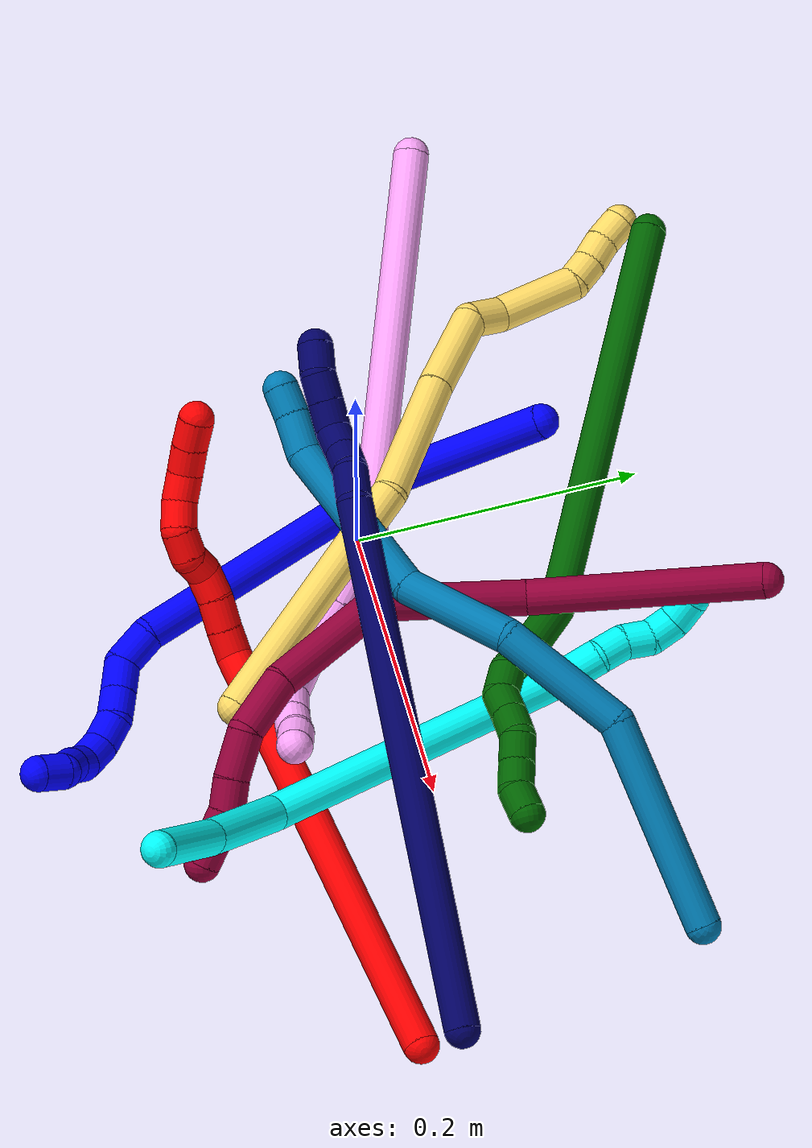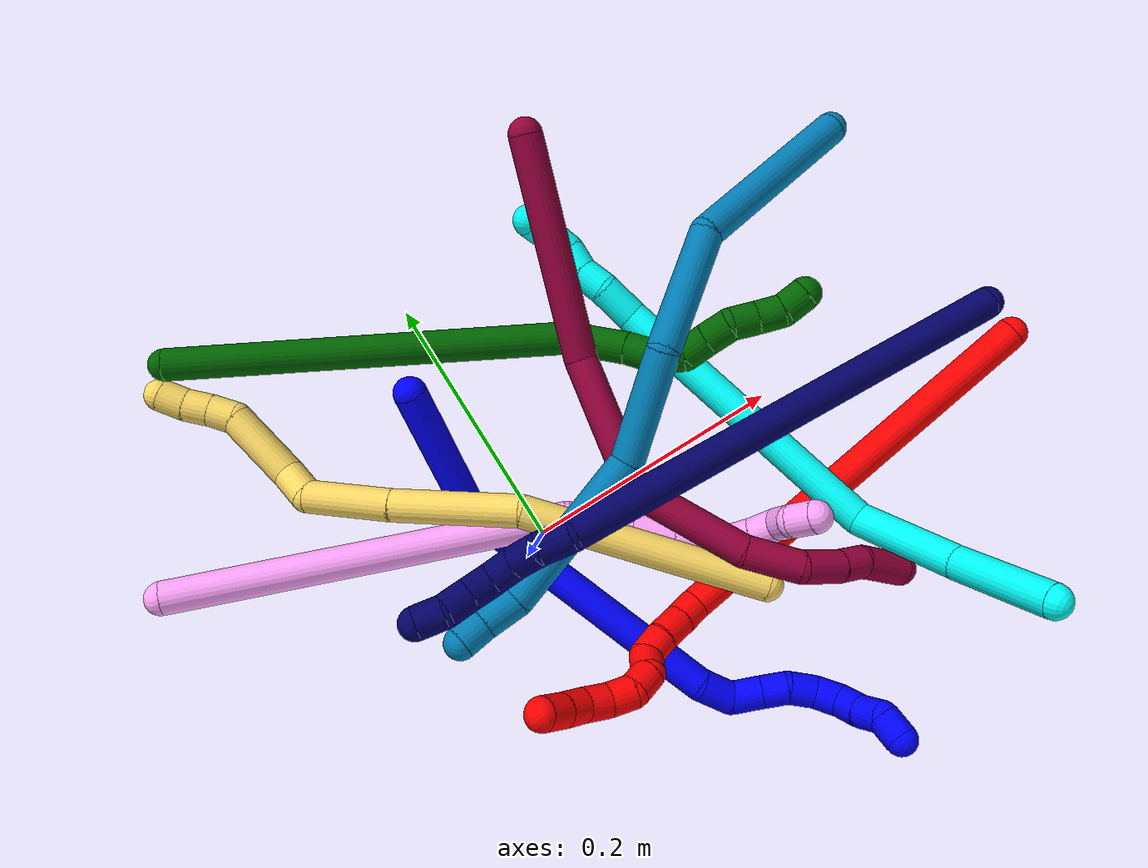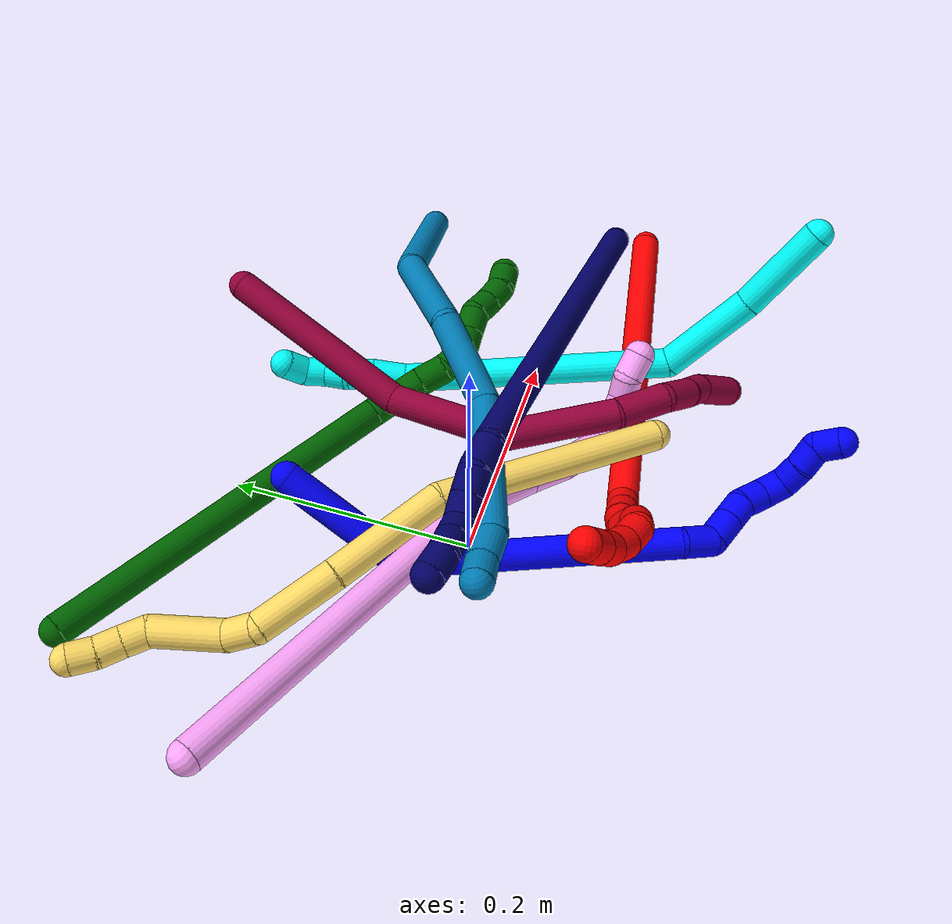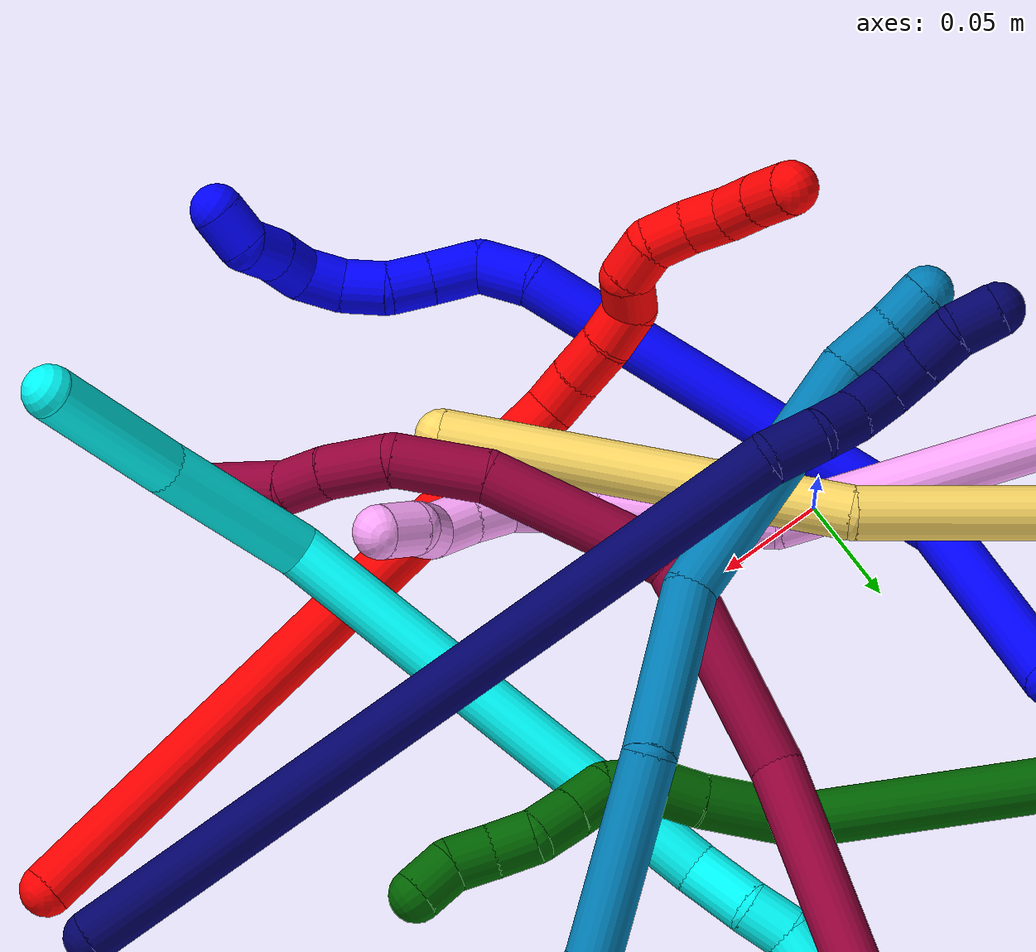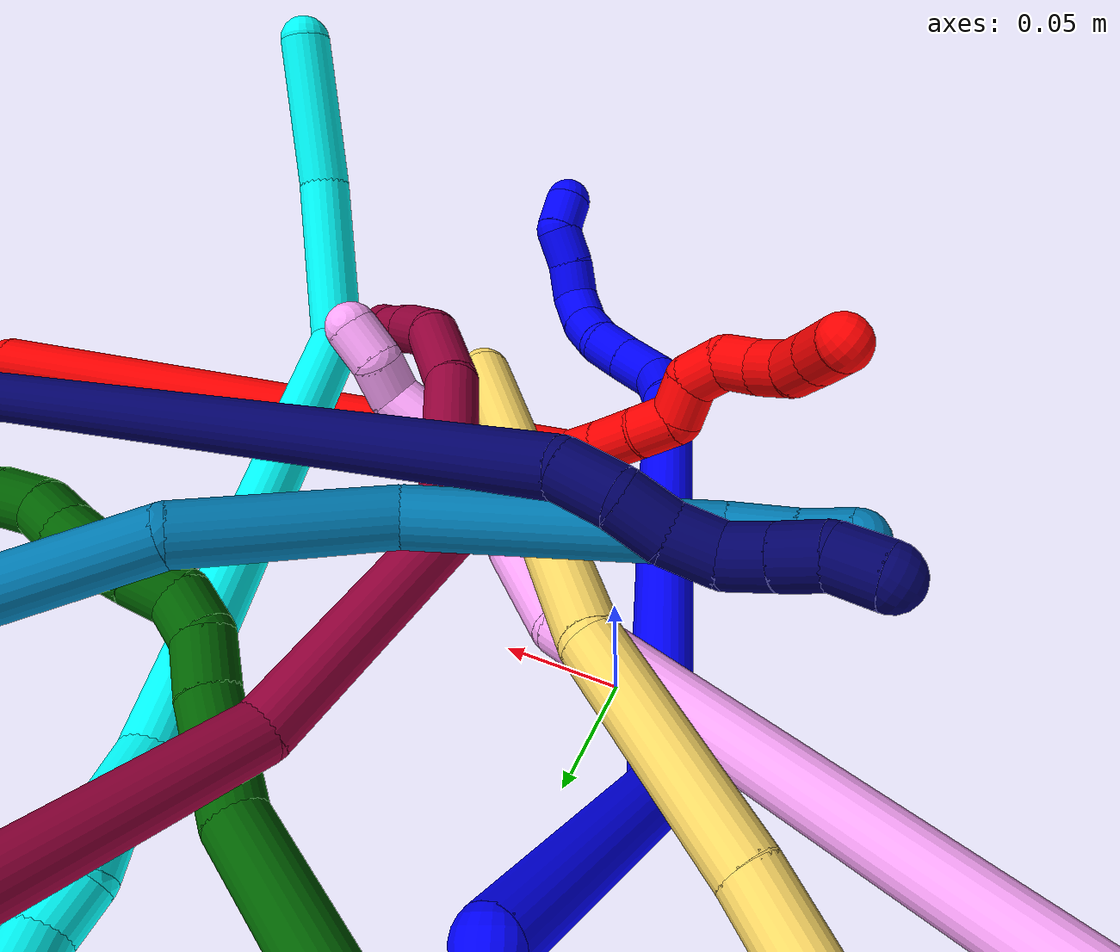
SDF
<sdf version="1.7">
 <world name="default">
  <plugin name="TubeGeneratorPlugin" filename="libtube_generator_plugin.so"/>
  <model name="photoneo_s_sensor">
   <static>1</static>
   <pose>0 0 2 1.57079 1.57079 3.14159</pose>
   <link name="link">
    <inertial><mass>0.1</mass></inertial>
    <sensor name="sensor" type="depth">
     <update_rate>30</update_rate>
     <camera>
      <horizontal_fov>1.22</horizontal_fov>
      <image><width>1920</width><height>1200</height><format>B8G8R8</format></image>
      <clip><near>0.1</near><far>4</far></clip>
      <depth_camera><output>points</output></depth_camera>
     </camera>
     <plugin name="camera_plugin" filename="libgazebo_ros_depth_camera.so">
      <baseline>0.2</baseline>
      <alwaysOn>1</alwaysOn>
      <updateRate>0.0</updateRate>
      <cameraName>camera_ir</cameraName>
      <imageTopicName>/camera/color/image_raw</imageTopicName>
      <cameraInfoTopicName>/camera/color/camera_info</cameraInfoTopicName>
      <depthImageTopicName>/camera/depth/image_raw</depthImageTopicName>
      <depthImageCameraInfoTopicName>/camera/depth/camera_info</depthImageCameraInfoTopicName>
      <pointCloudTopicName>/camera/depth/points</pointCloudTopicName>
      <frameName>fr_optical</frameName>
      <pointCloudCutoff>0.1</pointCloudCutoff>
      <pointCloudCutoffMax>2.0</pointCloudCutoffMax>
      <distortionK1>0</distortionK1>
      <distortionK2>0</distortionK2>
      <distortionK3>0</distortionK3>
      <distortionT1>0</distortionT1>
      <distortionT2>0</distortionT2>
      <CxPrime>0</CxPrime>
      <Cx>0</Cx>
      <Cy>0</Cy>
      <focalLength>0</focalLength>
      <hackBaseline>0</hackBaseline>
     </plugin>
    </sensor>
   </link>
  </model>
  <gravity>0 0 -9.8</gravity>
  <magnetic_field>6e-06 2.3e-05 -4.2e-05</magnetic_field>
  <atmosphere type="adiabatic"/>
  <physics name="default_physics" default="0" type="ode">
   <max_step_size>0.003</max_step_size>
   <real_time_factor>1</real_time_factor>
   <real_time_update_rate>1000</real_time_update_rate>
   <max_contacts>10000</max_contacts>
   <ode>
    <solver>
     <type>quick</type>
     <iters>100</iters>
     <sor>1.3</sor>
     <use_dynamic_moi_rescaling>0</use_dynamic_moi_rescaling>
    </solver>
    <constraints>
     <contact_max_correcting_vel>0</contact_max_correcting_vel>
     <contact_surface_layer>0.001</contact_surface_layer>
     <cfm>0</cfm>
     <erp>0.2</erp>
    </constraints>
   </ode>
  </physics>
  <scene><ambient>0.4 0.4 0.4 1</ambient><background>0.7 0.7 0.7 1</background><shadows>0</shadows></scene>
  <audio><device>default</device></audio>
  <spherical_coordinates>
   <surface_model>EARTH_WGS84</surface_model>
   <latitude_deg>0</latitude_deg>
   <longitude_deg>0</longitude_deg>
   <elevation>0</elevation>
   <heading_deg>0</heading_deg>
  </spherical_coordinates>
  <model name="bin">
   <static>1</static>
   <link name="bottom">
    <collision name="collision-bottom">
     <pose>0 0 -0.01 0 -0 0</pose>
     <geometry><box><size>0.8 0.6 0.02</size></box></geometry>
     <surface>
      <friction><ode><mu>100</mu><mu2>100</mu2></ode></friction>
      <contact><collide_bitmask>65535</collide_bitmask></contact>
     </surface>
    </collision>
   </link>
   <link name="west_wall">
    <collision name="collision-west_wall">
     <pose>-0.41 0 0.1 0 -0 0</pose>
     <geometry><box><size>0.02 0.6 0.2</size></box></geometry>
     <surface>
      <friction><ode><mu>100</mu><mu2>100</mu2></ode></friction>
      <contact><collide_bitmask>65535</collide_bitmask></contact>
     </surface>
    </collision>
   </link>
   <link name="east_wall">
    <collision name="collision-east_wall">
     <pose>0.41 0 0.1 0 -0 0</pose>
     <geometry><box><size>0.02 0.6 0.2</size></box></geometry>
     <surface>
      <friction><ode><mu>100</mu><mu2>100</mu2></ode></friction>
      <contact><collide_bitmask>65535</collide_bitmask></contact>
     </surface>
    </collision>
   </link>
   <link name="south_wall">
    <collision name="collision-south_wall">
     <pose>0 -0.31 0.1 0 -0 0</pose>
     <geometry><box><size>0.8 0.02 0.2</size></box></geometry>
     <surface>
      <friction><ode><mu>100</mu><mu2>100</mu2></ode></friction>
      <contact><collide_bitmask>65535</collide_bitmask></contact>
     </surface>
    </collision>
   </link>
   <link name="north_wall">
    <collision name="collision-north_wall">
     <pose>0 0.31 0.1 0 -0 0</pose>
     <geometry><box><size>0.8 0.02 0.2</size></box></geometry>
     <surface>
      <friction><ode><mu>100</mu><mu2>100</mu2></ode></friction>
      <contact><collide_bitmask>65535</collide_bitmask></contact>
     </surface>
    </collision>
   </link>
  </model>
  <model name="1">
   <static>0</static>
   <link name="1">
    <collision name="collision-cylinder-e_1_1_4">
     <pose>-0.000357 -0.046906 0.027877 1.03456 -0.006539 -0.00372</pose>
     <geometry><cylinder><radius>0.0125</radius><length>0.109132</length></cylinder></geometry>
     <surface>
      <friction><ode><mu>1.16</mu><mu2>1.16</mu2><slip1>0</slip1><slip2>0</slip2></ode></friction>
      <contact><ode><kp>1e+06</kp><kd>1</kd><max_vel>0</max_vel><min_depth>0.001</min_depth></ode></contact>
     </surface>
    </collision>
    <visual name="visual-cylinder-e_1_1_4">
     <pose>-0.000357 -0.046906 0.027877 1.03456 -0.006539 -0.00372</pose>
     <geometry><cylinder><radius>0.0125</radius><length>0.109132</length></cylinder></geometry>
     <material><ambient>0 0 1 1</ambient></material>
    </visual>
    <collision name="collision-cylinder-e_2_4_5">
     <pose>0.01714 -0.127623 0.157566 0.320632 0.164912 0.026726</pose>
     <geometry><cylinder><radius>0.0125</radius><length>0.217507</length></cylinder></geometry>
     <surface>
      <friction><ode><mu>1.16</mu><mu2>1.16</mu2><slip1>0</slip1><slip2>0</slip2></ode></friction>
      <contact><ode><kp>1e+06</kp><kd>1</kd><max_vel>0</max_vel><min_depth>0.001</min_depth></ode></contact>
     </surface>
    </collision>
    <visual name="visual-cylinder-e_2_4_5">
     <pose>0.01714 -0.127623 0.157566 0.320632 0.164912 0.026726</pose>
     <geometry><cylinder><radius>0.0125</radius><length>0.217507</length></cylinder></geometry>
     <material><ambient>0 0 1 1</ambient></material>
    </visual>
    <collision name="collision-cylinder-e_3_5_6">
     <pose>0.041081 -0.167195 0.270198 0.489226 0.46085 0.11698</pose>
     <geometry><cylinder><radius>0.0125</radius><length>0.027375</length></cylinder></geometry>
     <surface>
      <friction><ode><mu>1.16</mu><mu2>1.16</mu2><slip1>0</slip1><slip2>0</slip2></ode></friction>
      <contact><ode><kp>1e+06</kp><kd>1</kd><max_vel>0</max_vel><min_depth>0.001</min_depth></ode></contact>
     </surface>
    </collision>
    <visual name="visual-cylinder-e_3_5_6">
     <pose>0.041081 -0.167195 0.270198 0.489226 0.46085 0.11698</pose>
     <geometry><cylinder><radius>0.0125</radius><length>0.027375</length></cylinder></geometry>
     <material><ambient>0 0 1 1</ambient></material>
    </visual>
    <collision name="collision-cylinder-e_4_6_7">
     <pose>0.056261 -0.171053 0.288681 -0.243453 0.855915 -0.111488</pose>
     <geometry><cylinder><radius>0.0125</radius><length>0.024083</length></cylinder></geometry>
     <surface>
      <friction><ode><mu>1.16</mu><mu2>1.16</mu2><slip1>0</slip1><slip2>0</slip2></ode></friction>
      <contact><ode><kp>1e+06</kp><kd>1</kd><max_vel>0</max_vel><min_depth>0.001</min_depth></ode></contact>
     </surface>
    </collision>
    <visual name="visual-cylinder-e_4_6_7">
     <pose>0.056261 -0.171053 0.288681 -0.243453 0.855915 -0.111488</pose>
     <geometry><cylinder><radius>0.0125</radius><length>0.024083</length></cylinder></geometry>
     <material><ambient>0 0 1 1</ambient></material>
    </visual>
    <collision name="collision-cylinder-e_5_7_8">
     <pose>0.072636 -0.167251 0.302951 -0.279819 0.813886 -0.121247</pose>
     <geometry><cylinder><radius>0.0125</radius><length>0.020031</length></cylinder></geometry>
     <surface>
      <friction><ode><mu>1.16</mu><mu2>1.16</mu2><slip1>0</slip1><slip2>0</slip2></ode></friction>
      <contact><ode><kp>1e+06</kp><kd>1</kd><max_vel>0</max_vel><min_depth>0.001</min_depth></ode></contact>
     </surface>
    </collision>
    <visual name="visual-cylinder-e_5_7_8">
     <pose>0.072636 -0.167251 0.302951 -0.279819 0.813886 -0.121247</pose>
     <geometry><cylinder><radius>0.0125</radius><length>0.020031</length></cylinder></geometry>
     <material><ambient>0 0 1 1</ambient></material>
    </visual>
    <collision name="collision-cylinder-e_6_8_9">
     <pose>0.086161 -0.166774 0.317898 0.168954 0.636048 0.055738</pose>
     <geometry><cylinder><radius>0.0125</radius><length>0.021025</length></cylinder></geometry>
     <surface>
      <friction><ode><mu>1.16</mu><mu2>1.16</mu2><slip1>0</slip1><slip2>0</slip2></ode></friction>
      <contact><ode><kp>1e+06</kp><kd>1</kd><max_vel>0</max_vel><min_depth>0.001</min_depth></ode></contact>
     </surface>
    </collision>
    <visual name="visual-cylinder-e_6_8_9">
     <pose>0.086161 -0.166774 0.317898 0.168954 0.636048 0.055738</pose>
     <geometry><cylinder><radius>0.0125</radius><length>0.021025</length></cylinder></geometry>
     <material><ambient>0 0 1 1</ambient></material>
    </visual>
    <collision name="collision-cylinder-e_7_9_10">
     <pose>0.095779 -0.167617 0.335905 -0.05977 0.335104 -0.010112</pose>
     <geometry><cylinder><radius>0.0125</radius><length>0.020519</length></cylinder></geometry>
     <surface>
      <friction><ode><mu>1.16</mu><mu2>1.16</mu2><slip1>0</slip1><slip2>0</slip2></ode></friction>
      <contact><ode><kp>1e+06</kp><kd>1</kd><max_vel>0</max_vel><min_depth>0.001</min_depth></ode></contact>
     </surface>
    </collision>
    <visual name="visual-cylinder-e_7_9_10">
     <pose>0.095779 -0.167617 0.335905 -0.05977 0.335104 -0.010112</pose>
     <geometry><cylinder><radius>0.0125</radius><length>0.020519</length></cylinder></geometry>
     <material><ambient>0 0 1 1</ambient></material>
    </visual>
    <collision name="collision-cylinder-e_8_10_11">
     <pose>0.097907 -0.161779 0.354082 -0.553845 -0.123947 0.03527</pose>
     <geometry><cylinder><radius>0.0125</radius><length>0.020155</length></cylinder></geometry>
     <surface>
      <friction><ode><mu>1.16</mu><mu2>1.16</mu2><slip1>0</slip1><slip2>0</slip2></ode></friction>
      <contact><ode><kp>1e+06</kp><kd>1</kd><max_vel>0</max_vel><min_depth>0.001</min_depth></ode></contact>
     </surface>
    </collision>
    <visual name="visual-cylinder-e_8_10_11">
     <pose>0.097907 -0.161779 0.354082 -0.553845 -0.123947 0.03527</pose>
     <geometry><cylinder><radius>0.0125</radius><length>0.020155</length></cylinder></geometry>
     <material><ambient>0 0 1 1</ambient></material>
    </visual>
    <collision name="collision-cylinder-e_9_11_12">
     <pose>0.096984 -0.150346 0.370517 -0.661403 0.032037 -0.011</pose>
     <geometry><cylinder><radius>0.0125</radius><length>0.020109</length></cylinder></geometry>
     <surface>
      <friction><ode><mu>1.16</mu><mu2>1.16</mu2><slip1>0</slip1><slip2>0</slip2></ode></friction>
      <contact><ode><kp>1e+06</kp><kd>1</kd><max_vel>0</max_vel><min_depth>0.001</min_depth></ode></contact>
     </surface>
    </collision>
    <visual name="visual-cylinder-e_9_11_12">
     <pose>0.096984 -0.150346 0.370517 -0.661403 0.032037 -0.011</pose>
     <geometry><cylinder><radius>0.0125</radius><length>0.020109</length></cylinder></geometry>
     <material><ambient>0 0 1 1</ambient></material>
    </visual>
    <collision name="collision-cylinder-e_10_12_2">
     <pose>0.094641 -0.144357 0.388117 0.01888 -0.268816 -0.002553</pose>
     <geometry><cylinder><radius>0.0125</radius><length>0.020064</length></cylinder></geometry>
     <surface>
      <friction><ode><mu>1.16</mu><mu2>1.16</mu2><slip1>0</slip1><slip2>0</slip2></ode></friction>
      <contact><ode><kp>1e+06</kp><kd>1</kd><max_vel>0</max_vel><min_depth>0.001</min_depth></ode></contact>
     </surface>
    </collision>
    <visual name="visual-cylinder-e_10_12_2">
     <pose>0.094641 -0.144357 0.388117 0.01888 -0.268816 -0.002553</pose>
     <geometry><cylinder><radius>0.0125</radius><length>0.020064</length></cylinder></geometry>
     <material><ambient>0 0 1 1</ambient></material>
    </visual>
    <collision name="collision-sphere-2">
     <pose>0.091977 -0.144539 0.397787 0 -0 0</pose>
     <geometry><sphere><radius>0.0125</radius></sphere></geometry>
     <surface>
      <friction><ode><mu>1.16</mu><mu2>1.16</mu2><slip1>0</slip1><slip2>0</slip2></ode></friction>
      <contact><ode><kp>1e+06</kp><kd>1</kd><max_vel>0</max_vel><min_depth>0.001</min_depth></ode></contact>
     </surface>
    </collision>
    <visual name="visual-sphere-2">
     <pose>0.091977 -0.144539 0.397787 0 -0 0</pose>
     <geometry><sphere><radius>0.0125</radius></sphere></geometry>
     <material><ambient>0 0 1 1</ambient></material>
    </visual>
    <collision name="collision-sphere-12">
     <pose>0.097306 -0.144174 0.378447 0 -0 0</pose>
     <geometry><sphere><radius>0.0125</radius></sphere></geometry>
     <surface>
      <friction><ode><mu>1.16</mu><mu2>1.16</mu2><slip1>0</slip1><slip2>0</slip2></ode></friction>
      <contact><ode><kp>1e+06</kp><kd>1</kd><max_vel>0</max_vel><min_depth>0.001</min_depth></ode></contact>
     </surface>
    </collision>
    <visual name="visual-sphere-12">
     <pose>0.097306 -0.144174 0.378447 0 -0 0</pose>
     <geometry><sphere><radius>0.0125</radius></sphere></geometry>
     <material><ambient>0 0 1 1</ambient></material>
    </visual>
    <collision name="collision-sphere-11">
     <pose>0.096662 -0.156519 0.362587 0 -0 0</pose>
     <geometry><sphere><radius>0.0125</radius></sphere></geometry>
     <surface>
      <friction><ode><mu>1.16</mu><mu2>1.16</mu2><slip1>0</slip1><slip2>0</slip2></ode></friction>
      <contact><ode><kp>1e+06</kp><kd>1</kd><max_vel>0</max_vel><min_depth>0.001</min_depth></ode></contact>
     </surface>
    </collision>
    <visual name="visual-sphere-11">
     <pose>0.096662 -0.156519 0.362587 0 -0 0</pose>
     <geometry><sphere><radius>0.0125</radius></sphere></geometry>
     <material><ambient>0 0 1 1</ambient></material>
    </visual>
    <collision name="collision-sphere-10">
     <pose>0.099153 -0.167038 0.345577 0 -0 0</pose>
     <geometry><sphere><radius>0.0125</radius></sphere></geometry>
     <surface>
      <friction><ode><mu>1.16</mu><mu2>1.16</mu2><slip1>0</slip1><slip2>0</slip2></ode></friction>
      <contact><ode><kp>1e+06</kp><kd>1</kd><max_vel>0</max_vel><min_depth>0.001</min_depth></ode></contact>
     </surface>
    </collision>
    <visual name="visual-sphere-10">
     <pose>0.099153 -0.167038 0.345577 0 -0 0</pose>
     <geometry><sphere><radius>0.0125</radius></sphere></geometry>
     <material><ambient>0 0 1 1</ambient></material>
    </visual>
    <collision name="collision-sphere-9">
     <pose>0.092405 -0.168196 0.326234 0 -0 0</pose>
     <geometry><sphere><radius>0.0125</radius></sphere></geometry>
     <surface>
      <friction><ode><mu>1.16</mu><mu2>1.16</mu2><slip1>0</slip1><slip2>0</slip2></ode></friction>
      <contact><ode><kp>1e+06</kp><kd>1</kd><max_vel>0</max_vel><min_depth>0.001</min_depth></ode></contact>
     </surface>
    </collision>
    <visual name="visual-sphere-9">
     <pose>0.092405 -0.168196 0.326234 0 -0 0</pose>
     <geometry><sphere><radius>0.0125</radius></sphere></geometry>
     <material><ambient>0 0 1 1</ambient></material>
    </visual>
    <collision name="collision-sphere-4">
     <pose>-0.000714 -0.093812 0.055755 0 -0 0</pose>
     <geometry><sphere><radius>0.0125</radius></sphere></geometry>
     <surface>
      <friction><ode><mu>1.16</mu><mu2>1.16</mu2><slip1>0</slip1><slip2>0</slip2></ode></friction>
      <contact><ode><kp>1e+06</kp><kd>1</kd><max_vel>0</max_vel><min_depth>0.001</min_depth></ode></contact>
     </surface>
    </collision>
    <visual name="visual-sphere-4">
     <pose>-0.000714 -0.093812 0.055755 0 -0 0</pose>
     <geometry><sphere><radius>0.0125</radius></sphere></geometry>
     <material><ambient>0 0 1 1</ambient></material>
    </visual>
    <collision name="collision-sphere-1">
     <geometry><sphere><radius>0.0125</radius></sphere></geometry>
     <surface>
      <friction><ode><mu>1.16</mu><mu2>1.16</mu2><slip1>0</slip1><slip2>0</slip2></ode></friction>
      <contact><ode><kp>1e+06</kp><kd>1</kd><max_vel>0</max_vel><min_depth>0.001</min_depth></ode></contact>
     </surface>
    </collision>
    <visual name="visual-sphere-1">
     <geometry><sphere><radius>0.0125</radius></sphere></geometry>
     <material><ambient>0 0 1 1</ambient></material>
    </visual>
    <collision name="collision-sphere-8">
     <pose>0.079916 -0.165352 0.309561 0 -0 0</pose>
     <geometry><sphere><radius>0.0125</radius></sphere></geometry>
     <surface>
      <friction><ode><mu>1.16</mu><mu2>1.16</mu2><slip1>0</slip1><slip2>0</slip2></ode></friction>
      <contact><ode><kp>1e+06</kp><kd>1</kd><max_vel>0</max_vel><min_depth>0.001</min_depth></ode></contact>
     </surface>
    </collision>
    <visual name="visual-sphere-8">
     <pose>0.079916 -0.165352 0.309561 0 -0 0</pose>
     <geometry><sphere><radius>0.0125</radius></sphere></geometry>
     <material><ambient>0 0 1 1</ambient></material>
    </visual>
    <collision name="collision-sphere-5">
     <pose>0.034994 -0.161433 0.259377 0 -0 0</pose>
     <geometry><sphere><radius>0.0125</radius></sphere></geometry>
     <surface>
      <friction><ode><mu>1.16</mu><mu2>1.16</mu2><slip1>0</slip1><slip2>0</slip2></ode></friction>
      <contact><ode><kp>1e+06</kp><kd>1</kd><max_vel>0</max_vel><min_depth>0.001</min_depth></ode></contact>
     </surface>
    </collision>
    <visual name="visual-sphere-5">
     <pose>0.034994 -0.161433 0.259377 0 -0 0</pose>
     <geometry><sphere><radius>0.0125</radius></sphere></geometry>
     <material><ambient>0 0 1 1</ambient></material>
    </visual>
    <collision name="collision-sphere-6">
     <pose>0.047168 -0.172956 0.28102 0 -0 0</pose>
     <geometry><sphere><radius>0.0125</radius></sphere></geometry>
     <surface>
      <friction><ode><mu>1.16</mu><mu2>1.16</mu2><slip1>0</slip1><slip2>0</slip2></ode></friction>
      <contact><ode><kp>1e+06</kp><kd>1</kd><max_vel>0</max_vel><min_depth>0.001</min_depth></ode></contact>
     </surface>
    </collision>
    <visual name="visual-sphere-6">
     <pose>0.047168 -0.172956 0.28102 0 -0 0</pose>
     <geometry><sphere><radius>0.0125</radius></sphere></geometry>
     <material><ambient>0 0 1 1</ambient></material>
    </visual>
    <collision name="collision-sphere-7">
     <pose>0.065355 -0.16915 0.296342 0 -0 0</pose>
     <geometry><sphere><radius>0.0125</radius></sphere></geometry>
     <surface>
      <friction><ode><mu>1.16</mu><mu2>1.16</mu2><slip1>0</slip1><slip2>0</slip2></ode></friction>
      <contact><ode><kp>1e+06</kp><kd>1</kd><max_vel>0</max_vel><min_depth>0.001</min_depth></ode></contact>
     </surface>
    </collision>
    <visual name="visual-sphere-7">
     <pose>0.065355 -0.16915 0.296342 0 -0 0</pose>
     <geometry><sphere><radius>0.0125</radius></sphere></geometry>
     <material><ambient>0 0 1 1</ambient></material>
    </visual>
    <inertial>
     <pose>0.034446 -0.122101 0.187364 0 -0 0</pose>
     <mass>0.5</mass>
     <inertia>
      <ixx>0.001008</ixx>
      <ixy>0</ixy>
      <ixz>0</ixz>
      <iyy>0.000904</iyy>
      <iyz>0</iyz>
      <izz>0.00025</izz>
     </inertia>
    </inertial>
   </link>
   <pose>-0.023334 0.137793 0.064439 1.12181 0.487426 0.164812</pose>
  </model>
  <model name="2">
   <static>0</static>
   <link name="2">
    <collision name="collision-cylinder-e_1_1_4">
     <pose>-0.099269 -0.007704 -0.123444 3.07927 -0.676323 -2.96477</pose>
     <geometry><cylinder><radius>0.0125</radius><length>0.317188</length></cylinder></geometry>
     <surface>
      <friction><ode><mu>1.16</mu><mu2>1.16</mu2><slip1>0</slip1><slip2>0</slip2></ode></friction>
      <contact><ode><kp>1e+06</kp><kd>1</kd><max_vel>0</max_vel><min_depth>0.001</min_depth></ode></contact>
     </surface>
    </collision>
    <visual name="visual-cylinder-e_1_1_4">
     <pose>-0.099269 -0.007704 -0.123444 3.07927 -0.676323 -2.96477</pose>
     <geometry><cylinder><radius>0.0125</radius><length>0.317188</length></cylinder></geometry>
     <material><ambient>1 0 0 1</ambient></material>
    </visual>
    <collision name="collision-cylinder-e_2_4_5">
     <pose>-0.208018 -0.015647 -0.25033 3.07217 -1.22181 -3.04249</pose>
     <geometry><cylinder><radius>0.0125</radius><length>0.020178</length></cylinder></geometry>
     <surface>
      <friction><ode><mu>1.16</mu><mu2>1.16</mu2><slip1>0</slip1><slip2>0</slip2></ode></friction>
      <contact><ode><kp>1e+06</kp><kd>1</kd><max_vel>0</max_vel><min_depth>0.001</min_depth></ode></contact>
     </surface>
    </collision>
    <visual name="visual-cylinder-e_2_4_5">
     <pose>-0.208018 -0.015647 -0.25033 3.07217 -1.22181 -3.04249</pose>
     <geometry><cylinder><radius>0.0125</radius><length>0.020178</length></cylinder></geometry>
     <material><ambient>1 0 0 1</ambient></material>
    </visual>
    <collision name="collision-cylinder-e_3_5_6">
     <pose>-0.228354 -0.015614 -0.256809 -3.05229 -1.29688 3.02379</pose>
     <geometry><cylinder><radius>0.0125</radius><length>0.02255</length></cylinder></geometry>
     <surface>
      <friction><ode><mu>1.16</mu><mu2>1.16</mu2><slip1>0</slip1><slip2>0</slip2></ode></friction>
      <contact><ode><kp>1e+06</kp><kd>1</kd><max_vel>0</max_vel><min_depth>0.001</min_depth></ode></contact>
     </surface>
    </collision>
    <visual name="visual-cylinder-e_3_5_6">
     <pose>-0.228354 -0.015614 -0.256809 -3.05229 -1.29688 3.02379</pose>
     <geometry><cylinder><radius>0.0125</radius><length>0.02255</length></cylinder></geometry>
     <material><ambient>1 0 0 1</ambient></material>
    </visual>
    <collision name="collision-cylinder-e_4_6_7">
     <pose>-0.248623 -0.016423 -0.263164 2.82643 -1.21596 -2.69263</pose>
     <geometry><cylinder><radius>0.0125</radius><length>0.02008</length></cylinder></geometry>
     <surface>
      <friction><ode><mu>1.16</mu><mu2>1.16</mu2><slip1>0</slip1><slip2>0</slip2></ode></friction>
      <contact><ode><kp>1e+06</kp><kd>1</kd><max_vel>0</max_vel><min_depth>0.001</min_depth></ode></contact>
     </surface>
    </collision>
    <visual name="visual-cylinder-e_4_6_7">
     <pose>-0.248623 -0.016423 -0.263164 2.82643 -1.21596 -2.69263</pose>
     <geometry><cylinder><radius>0.0125</radius><length>0.02008</length></cylinder></geometry>
     <material><ambient>1 0 0 1</ambient></material>
    </visual>
    <collision name="collision-cylinder-e_5_7_8">
     <pose>-0.266471 -0.021397 -0.262771 0.809563 -1.00316 -0.461504</pose>
     <geometry><cylinder><radius>0.0125</radius><length>0.020003</length></cylinder></geometry>
     <surface>
      <friction><ode><mu>1.16</mu><mu2>1.16</mu2><slip1>0</slip1><slip2>0</slip2></ode></friction>
      <contact><ode><kp>1e+06</kp><kd>1</kd><max_vel>0</max_vel><min_depth>0.001</min_depth></ode></contact>
     </surface>
    </collision>
    <visual name="visual-cylinder-e_5_7_8">
     <pose>-0.266471 -0.021397 -0.262771 0.809563 -1.00316 -0.461504</pose>
     <geometry><cylinder><radius>0.0125</radius><length>0.020003</length></cylinder></geometry>
     <material><ambient>1 0 0 1</ambient></material>
    </visual>
    <collision name="collision-cylinder-e_6_8_9">
     <pose>-0.284694 -0.025765 -0.261043 2.90639 -1.36561 -2.85308</pose>
     <geometry><cylinder><radius>0.0125</radius><length>0.02</length></cylinder></geometry>
     <surface>
      <friction><ode><mu>1.16</mu><mu2>1.16</mu2><slip1>0</slip1><slip2>0</slip2></ode></friction>
      <contact><ode><kp>1e+06</kp><kd>1</kd><max_vel>0</max_vel><min_depth>0.001</min_depth></ode></contact>
     </surface>
    </collision>
    <visual name="visual-cylinder-e_6_8_9">
     <pose>-0.284694 -0.025765 -0.261043 2.90639 -1.36561 -2.85308</pose>
     <geometry><cylinder><radius>0.0125</radius><length>0.02</length></cylinder></geometry>
     <material><ambient>1 0 0 1</ambient></material>
    </visual>
    <collision name="collision-cylinder-e_7_9_10">
     <pose>-0.302246 -0.022595 -0.268169 -2.52517 -0.888558 1.96265</pose>
     <geometry><cylinder><radius>0.0125</radius><length>0.02</length></cylinder></geometry>
     <surface>
      <friction><ode><mu>1.16</mu><mu2>1.16</mu2><slip1>0</slip1><slip2>0</slip2></ode></friction>
      <contact><ode><kp>1e+06</kp><kd>1</kd><max_vel>0</max_vel><min_depth>0.001</min_depth></ode></contact>
     </surface>
    </collision>
    <visual name="visual-cylinder-e_7_9_10">
     <pose>-0.302246 -0.022595 -0.268169 -2.52517 -0.888558 1.96265</pose>
     <geometry><cylinder><radius>0.0125</radius><length>0.02</length></cylinder></geometry>
     <material><ambient>1 0 0 1</ambient></material>
    </visual>
    <collision name="collision-cylinder-e_8_10_11">
     <pose>-0.318296 -0.014059 -0.276032 -2.0781 -0.977022 1.46946</pose>
     <geometry><cylinder><radius>0.0125</radius><length>0.02</length></cylinder></geometry>
     <surface>
      <friction><ode><mu>1.16</mu><mu2>1.16</mu2><slip1>0</slip1><slip2>0</slip2></ode></friction>
      <contact><ode><kp>1e+06</kp><kd>1</kd><max_vel>0</max_vel><min_depth>0.001</min_depth></ode></contact>
     </surface>
    </collision>
    <visual name="visual-cylinder-e_8_10_11">
     <pose>-0.318296 -0.014059 -0.276032 -2.0781 -0.977022 1.46946</pose>
     <geometry><cylinder><radius>0.0125</radius><length>0.02</length></cylinder></geometry>
     <material><ambient>1 0 0 1</ambient></material>
    </visual>
    <collision name="collision-cylinder-e_9_11_12">
     <pose>-0.335699 -0.005065 -0.278477 -1.50433 -1.14694 1.08717</pose>
     <geometry><cylinder><radius>0.0125</radius><length>0.02</length></cylinder></geometry>
     <surface>
      <friction><ode><mu>1.16</mu><mu2>1.16</mu2><slip1>0</slip1><slip2>0</slip2></ode></friction>
      <contact><ode><kp>1e+06</kp><kd>1</kd><max_vel>0</max_vel><min_depth>0.001</min_depth></ode></contact>
     </surface>
    </collision>
    <visual name="visual-cylinder-e_9_11_12">
     <pose>-0.335699 -0.005065 -0.278477 -1.50433 -1.14694 1.08717</pose>
     <geometry><cylinder><radius>0.0125</radius><length>0.02</length></cylinder></geometry>
     <material><ambient>1 0 0 1</ambient></material>
    </visual>
    <collision name="collision-cylinder-e_10_12_2">
     <pose>-0.353707 0.003549 -0.277441 -1.40308 -1.09566 0.951953</pose>
     <geometry><cylinder><radius>0.0125</radius><length>0.02</length></cylinder></geometry>
     <surface>
      <friction><ode><mu>1.16</mu><mu2>1.16</mu2><slip1>0</slip1><slip2>0</slip2></ode></friction>
      <contact><ode><kp>1e+06</kp><kd>1</kd><max_vel>0</max_vel><min_depth>0.001</min_depth></ode></contact>
     </surface>
    </collision>
    <visual name="visual-cylinder-e_10_12_2">
     <pose>-0.353707 0.003549 -0.277441 -1.40308 -1.09566 0.951953</pose>
     <geometry><cylinder><radius>0.0125</radius><length>0.02</length></cylinder></geometry>
     <material><ambient>1 0 0 1</ambient></material>
    </visual>
    <collision name="collision-sphere-2">
     <pose>-0.3626 0.00806 -0.276677 0 -0 0</pose>
     <geometry><sphere><radius>0.0125</radius></sphere></geometry>
     <surface>
      <friction><ode><mu>1.16</mu><mu2>1.16</mu2><slip1>0</slip1><slip2>0</slip2></ode></friction>
      <contact><ode><kp>1e+06</kp><kd>1</kd><max_vel>0</max_vel><min_depth>0.001</min_depth></ode></contact>
     </surface>
    </collision>
    <visual name="visual-sphere-2">
     <pose>-0.3626 0.00806 -0.276677 0 -0 0</pose>
     <geometry><sphere><radius>0.0125</radius></sphere></geometry>
     <material><ambient>1 0 0 1</ambient></material>
    </visual>
    <collision name="collision-sphere-12">
     <pose>-0.344815 -0.000961 -0.278204 0 -0 0</pose>
     <geometry><sphere><radius>0.0125</radius></sphere></geometry>
     <surface>
      <friction><ode><mu>1.16</mu><mu2>1.16</mu2><slip1>0</slip1><slip2>0</slip2></ode></friction>
      <contact><ode><kp>1e+06</kp><kd>1</kd><max_vel>0</max_vel><min_depth>0.001</min_depth></ode></contact>
     </surface>
    </collision>
    <visual name="visual-sphere-12">
     <pose>-0.344815 -0.000961 -0.278204 0 -0 0</pose>
     <geometry><sphere><radius>0.0125</radius></sphere></geometry>
     <material><ambient>1 0 0 1</ambient></material>
    </visual>
    <collision name="collision-sphere-11">
     <pose>-0.326584 -0.009169 -0.278751 0 -0 0</pose>
     <geometry><sphere><radius>0.0125</radius></sphere></geometry>
     <surface>
      <friction><ode><mu>1.16</mu><mu2>1.16</mu2><slip1>0</slip1><slip2>0</slip2></ode></friction>
      <contact><ode><kp>1e+06</kp><kd>1</kd><max_vel>0</max_vel><min_depth>0.001</min_depth></ode></contact>
     </surface>
    </collision>
    <visual name="visual-sphere-11">
     <pose>-0.326584 -0.009169 -0.278751 0 -0 0</pose>
     <geometry><sphere><radius>0.0125</radius></sphere></geometry>
     <material><ambient>1 0 0 1</ambient></material>
    </visual>
    <collision name="collision-sphere-10">
     <pose>-0.310007 -0.018949 -0.273314 0 -0 0</pose>
     <geometry><sphere><radius>0.0125</radius></sphere></geometry>
     <surface>
      <friction><ode><mu>1.16</mu><mu2>1.16</mu2><slip1>0</slip1><slip2>0</slip2></ode></friction>
      <contact><ode><kp>1e+06</kp><kd>1</kd><max_vel>0</max_vel><min_depth>0.001</min_depth></ode></contact>
     </surface>
    </collision>
    <visual name="visual-sphere-10">
     <pose>-0.310007 -0.018949 -0.273314 0 -0 0</pose>
     <geometry><sphere><radius>0.0125</radius></sphere></geometry>
     <material><ambient>1 0 0 1</ambient></material>
    </visual>
    <collision name="collision-sphere-9">
     <pose>-0.294484 -0.02624 -0.263024 0 -0 0</pose>
     <geometry><sphere><radius>0.0125</radius></sphere></geometry>
     <surface>
      <friction><ode><mu>1.16</mu><mu2>1.16</mu2><slip1>0</slip1><slip2>0</slip2></ode></friction>
      <contact><ode><kp>1e+06</kp><kd>1</kd><max_vel>0</max_vel><min_depth>0.001</min_depth></ode></contact>
     </surface>
    </collision>
    <visual name="visual-sphere-9">
     <pose>-0.294484 -0.02624 -0.263024 0 -0 0</pose>
     <geometry><sphere><radius>0.0125</radius></sphere></geometry>
     <material><ambient>1 0 0 1</ambient></material>
    </visual>
    <collision name="collision-sphere-4">
     <pose>-0.198538 -0.015407 -0.246888 0 -0 0</pose>
     <geometry><sphere><radius>0.0125</radius></sphere></geometry>
     <surface>
      <friction><ode><mu>1.16</mu><mu2>1.16</mu2><slip1>0</slip1><slip2>0</slip2></ode></friction>
      <contact><ode><kp>1e+06</kp><kd>1</kd><max_vel>0</max_vel><min_depth>0.001</min_depth></ode></contact>
     </surface>
    </collision>
    <visual name="visual-sphere-4">
     <pose>-0.198538 -0.015407 -0.246888 0 -0 0</pose>
     <geometry><sphere><radius>0.0125</radius></sphere></geometry>
     <material><ambient>1 0 0 1</ambient></material>
    </visual>
    <collision name="collision-sphere-1">
     <geometry><sphere><radius>0.0125</radius></sphere></geometry>
     <surface>
      <friction><ode><mu>1.16</mu><mu2>1.16</mu2><slip1>0</slip1><slip2>0</slip2></ode></friction>
      <contact><ode><kp>1e+06</kp><kd>1</kd><max_vel>0</max_vel><min_depth>0.001</min_depth></ode></contact>
     </surface>
    </collision>
    <visual name="visual-sphere-1">
     <geometry><sphere><radius>0.0125</radius></sphere></geometry>
     <material><ambient>1 0 0 1</ambient></material>
    </visual>
    <collision name="collision-sphere-8">
     <pose>-0.274903 -0.02529 -0.259062 0 -0 0</pose>
     <geometry><sphere><radius>0.0125</radius></sphere></geometry>
     <surface>
      <friction><ode><mu>1.16</mu><mu2>1.16</mu2><slip1>0</slip1><slip2>0</slip2></ode></friction>
      <contact><ode><kp>1e+06</kp><kd>1</kd><max_vel>0</max_vel><min_depth>0.001</min_depth></ode></contact>
     </surface>
    </collision>
    <visual name="visual-sphere-8">
     <pose>-0.274903 -0.02529 -0.259062 0 -0 0</pose>
     <geometry><sphere><radius>0.0125</radius></sphere></geometry>
     <material><ambient>1 0 0 1</ambient></material>
    </visual>
    <collision name="collision-sphere-5">
     <pose>-0.217499 -0.015886 -0.253772 0 -0 0</pose>
     <geometry><sphere><radius>0.0125</radius></sphere></geometry>
     <surface>
      <friction><ode><mu>1.16</mu><mu2>1.16</mu2><slip1>0</slip1><slip2>0</slip2></ode></friction>
      <contact><ode><kp>1e+06</kp><kd>1</kd><max_vel>0</max_vel><min_depth>0.001</min_depth></ode></contact>
     </surface>
    </collision>
    <visual name="visual-sphere-5">
     <pose>-0.217499 -0.015886 -0.253772 0 -0 0</pose>
     <geometry><sphere><radius>0.0125</radius></sphere></geometry>
     <material><ambient>1 0 0 1</ambient></material>
    </visual>
    <collision name="collision-sphere-6">
     <pose>-0.239209 -0.015342 -0.259847 0 -0 0</pose>
     <geometry><sphere><radius>0.0125</radius></sphere></geometry>
     <surface>
      <friction><ode><mu>1.16</mu><mu2>1.16</mu2><slip1>0</slip1><slip2>0</slip2></ode></friction>
      <contact><ode><kp>1e+06</kp><kd>1</kd><max_vel>0</max_vel><min_depth>0.001</min_depth></ode></contact>
     </surface>
    </collision>
    <visual name="visual-sphere-6">
     <pose>-0.239209 -0.015342 -0.259847 0 -0 0</pose>
     <geometry><sphere><radius>0.0125</radius></sphere></geometry>
     <material><ambient>1 0 0 1</ambient></material>
    </visual>
    <collision name="collision-sphere-7">
     <pose>-0.258038 -0.017504 -0.26648 0 -0 0</pose>
     <geometry><sphere><radius>0.0125</radius></sphere></geometry>
     <surface>
      <friction><ode><mu>1.16</mu><mu2>1.16</mu2><slip1>0</slip1><slip2>0</slip2></ode></friction>
      <contact><ode><kp>1e+06</kp><kd>1</kd><max_vel>0</max_vel><min_depth>0.001</min_depth></ode></contact>
     </surface>
    </collision>
    <visual name="visual-sphere-7">
     <pose>-0.258038 -0.017504 -0.26648 0 -0 0</pose>
     <geometry><sphere><radius>0.0125</radius></sphere></geometry>
     <material><ambient>1 0 0 1</ambient></material>
    </visual>
    <inertial>
     <pose>-0.166099 -0.010296 -0.175522 0 -0 0</pose>
     <mass>0.5</mass>
     <inertia>
      <ixx>-0.002445</ixx>
      <ixy>0</ixy>
      <ixz>0</ixz>
      <iyy>0.002291</iyy>
      <iyz>0</iyz>
      <izz>0.001791</izz>
     </inertia>
    </inertial>
   </link>
   <pose>0.385461 -0.059298 0.011498 0.030111 0.90186 0.124787</pose>
  </model>
  <model name="3">
   <static>0</static>
   <link name="3">
    <collision name="collision-cylinder-e_1_1_4">
     <pose>0.003171 -0.004151 -0.038146 3.0332 0.082456 1.30025</pose>
     <geometry><cylinder><radius>0.0125</radius><length>0.077004</length></cylinder></geometry>
     <surface>
      <friction><ode><mu>1.16</mu><mu2>1.16</mu2><slip1>0</slip1><slip2>0</slip2></ode></friction>
      <contact><ode><kp>1e+06</kp><kd>1</kd><max_vel>0</max_vel><min_depth>0.001</min_depth></ode></contact>
     </surface>
    </collision>
    <visual name="visual-cylinder-e_1_1_4">
     <pose>0.003171 -0.004151 -0.038146 3.0332 0.082456 1.30025</pose>
     <geometry><cylinder><radius>0.0125</radius><length>0.077004</length></cylinder></geometry>
     <material><ambient>0.003922 1 0.996078 1</ambient></material>
    </visual>
    <collision name="collision-cylinder-e_2_4_5">
     <pose>0.004731 -0.008436 -0.117848 3.13836 -0.038745 -2.97497</pose>
     <geometry><cylinder><radius>0.0125</radius><length>0.083175</length></cylinder></geometry>
     <surface>
      <friction><ode><mu>1.16</mu><mu2>1.16</mu2><slip1>0</slip1><slip2>0</slip2></ode></friction>
      <contact><ode><kp>1e+06</kp><kd>1</kd><max_vel>0</max_vel><min_depth>0.001</min_depth></ode></contact>
     </surface>
    </collision>
    <visual name="visual-cylinder-e_2_4_5">
     <pose>0.004731 -0.008436 -0.117848 3.13836 -0.038745 -2.97497</pose>
     <geometry><cylinder><radius>0.0125</radius><length>0.083175</length></cylinder></geometry>
     <material><ambient>0.003922 1 0.996078 1</ambient></material>
    </visual>
    <collision name="collision-cylinder-e_3_5_6">
     <pose>-0.037964 0.050481 -0.248231 -2.55489 -0.36766 1.10352</pose>
     <geometry><cylinder><radius>0.0125</radius><length>0.228608</length></cylinder></geometry>
     <surface>
      <friction><ode><mu>1.16</mu><mu2>1.16</mu2><slip1>0</slip1><slip2>0</slip2></ode></friction>
      <contact><ode><kp>1e+06</kp><kd>1</kd><max_vel>0</max_vel><min_depth>0.001</min_depth></ode></contact>
     </surface>
    </collision>
    <visual name="visual-cylinder-e_3_5_6">
     <pose>-0.037964 0.050481 -0.248231 -2.55489 -0.36766 1.10352</pose>
     <geometry><cylinder><radius>0.0125</radius><length>0.228608</length></cylinder></geometry>
     <material><ambient>0.003922 1 0.996078 1</ambient></material>
    </visual>
    <collision name="collision-cylinder-e_4_6_7">
     <pose>-0.086915 0.119063 -0.345754 -2.31036 -0.547523 1.13336</pose>
     <geometry><cylinder><radius>0.0125</radius><length>0.030219</length></cylinder></geometry>
     <surface>
      <friction><ode><mu>1.16</mu><mu2>1.16</mu2><slip1>0</slip1><slip2>0</slip2></ode></friction>
      <contact><ode><kp>1e+06</kp><kd>1</kd><max_vel>0</max_vel><min_depth>0.001</min_depth></ode></contact>
     </surface>
    </collision>
    <visual name="visual-cylinder-e_4_6_7">
     <pose>-0.086915 0.119063 -0.345754 -2.31036 -0.547523 1.13336</pose>
     <geometry><cylinder><radius>0.0125</radius><length>0.030219</length></cylinder></geometry>
     <material><ambient>0.003922 1 0.996078 1</ambient></material>
    </visual>
    <collision name="collision-cylinder-e_5_7_8">
     <pose>-0.099226 0.133405 -0.36265 -2.61104 -0.437307 1.37113</pose>
     <geometry><cylinder><radius>0.0125</radius><length>0.020993</length></cylinder></geometry>
     <surface>
      <friction><ode><mu>1.16</mu><mu2>1.16</mu2><slip1>0</slip1><slip2>0</slip2></ode></friction>
      <contact><ode><kp>1e+06</kp><kd>1</kd><max_vel>0</max_vel><min_depth>0.001</min_depth></ode></contact>
     </surface>
    </collision>
    <visual name="visual-cylinder-e_5_7_8">
     <pose>-0.099226 0.133405 -0.36265 -2.61104 -0.437307 1.37113</pose>
     <geometry><cylinder><radius>0.0125</radius><length>0.020993</length></cylinder></geometry>
     <material><ambient>0.003922 1 0.996078 1</ambient></material>
    </visual>
    <collision name="collision-cylinder-e_6_8_9">
     <pose>-0.105355 0.145247 -0.377762 -2.34755 -0.169238 0.399213</pose>
     <geometry><cylinder><radius>0.0125</radius><length>0.02</length></cylinder></geometry>
     <surface>
      <friction><ode><mu>1.16</mu><mu2>1.16</mu2><slip1>0</slip1><slip2>0</slip2></ode></friction>
      <contact><ode><kp>1e+06</kp><kd>1</kd><max_vel>0</max_vel><min_depth>0.001</min_depth></ode></contact>
     </surface>
    </collision>
    <visual name="visual-cylinder-e_6_8_9">
     <pose>-0.105355 0.145247 -0.377762 -2.34755 -0.169238 0.399213</pose>
     <geometry><cylinder><radius>0.0125</radius><length>0.02</length></cylinder></geometry>
     <material><ambient>0.003922 1 0.996078 1</ambient></material>
    </visual>
    <collision name="collision-cylinder-e_7_9_10">
     <pose>-0.112604 0.157768 -0.390907 -2.41956 -0.590095 1.35549</pose>
     <geometry><cylinder><radius>0.0125</radius><length>0.02</length></cylinder></geometry>
     <surface>
      <friction><ode><mu>1.16</mu><mu2>1.16</mu2><slip1>0</slip1><slip2>0</slip2></ode></friction>
      <contact><ode><kp>1e+06</kp><kd>1</kd><max_vel>0</max_vel><min_depth>0.001</min_depth></ode></contact>
     </surface>
    </collision>
    <visual name="visual-cylinder-e_7_9_10">
     <pose>-0.112604 0.157768 -0.390907 -2.41956 -0.590095 1.35549</pose>
     <geometry><cylinder><radius>0.0125</radius><length>0.02</length></cylinder></geometry>
     <material><ambient>0.003922 1 0.996078 1</ambient></material>
    </visual>
    <collision name="collision-cylinder-e_8_10_2">
     <pose>-0.126388 0.168756 -0.398637 -1.83633 -0.964861 1.20138</pose>
     <geometry><cylinder><radius>0.0125</radius><length>0.02</length></cylinder></geometry>
     <surface>
      <friction><ode><mu>1.16</mu><mu2>1.16</mu2><slip1>0</slip1><slip2>0</slip2></ode></friction>
      <contact><ode><kp>1e+06</kp><kd>1</kd><max_vel>0</max_vel><min_depth>0.001</min_depth></ode></contact>
     </surface>
    </collision>
    <visual name="visual-cylinder-e_8_10_2">
     <pose>-0.126388 0.168756 -0.398637 -1.83633 -0.964861 1.20138</pose>
     <geometry><cylinder><radius>0.0125</radius><length>0.02</length></cylinder></geometry>
     <material><ambient>0.003922 1 0.996078 1</ambient></material>
    </visual>
    <collision name="collision-sphere-2">
     <pose>-0.134608 0.174252 -0.400132 0 -0 0</pose>
     <geometry><sphere><radius>0.0125</radius></sphere></geometry>
     <surface>
      <friction><ode><mu>1.16</mu><mu2>1.16</mu2><slip1>0</slip1><slip2>0</slip2></ode></friction>
      <contact><ode><kp>1e+06</kp><kd>1</kd><max_vel>0</max_vel><min_depth>0.001</min_depth></ode></contact>
     </surface>
    </collision>
    <visual name="visual-sphere-2">
     <pose>-0.134608 0.174252 -0.400132 0 -0 0</pose>
     <geometry><sphere><radius>0.0125</radius></sphere></geometry>
     <material><ambient>0.003922 1 0.996078 1</ambient></material>
    </visual>
    <collision name="collision-sphere-10">
     <pose>-0.118169 0.16326 -0.397142 0 -0 0</pose>
     <geometry><sphere><radius>0.0125</radius></sphere></geometry>
     <surface>
      <friction><ode><mu>1.16</mu><mu2>1.16</mu2><slip1>0</slip1><slip2>0</slip2></ode></friction>
      <contact><ode><kp>1e+06</kp><kd>1</kd><max_vel>0</max_vel><min_depth>0.001</min_depth></ode></contact>
     </surface>
    </collision>
    <visual name="visual-sphere-10">
     <pose>-0.118169 0.16326 -0.397142 0 -0 0</pose>
     <geometry><sphere><radius>0.0125</radius></sphere></geometry>
     <material><ambient>0.003922 1 0.996078 1</ambient></material>
    </visual>
    <collision name="collision-sphere-9">
     <pose>-0.10704 0.152277 -0.384671 0 -0 0</pose>
     <geometry><sphere><radius>0.0125</radius></sphere></geometry>
     <surface>
      <friction><ode><mu>1.16</mu><mu2>1.16</mu2><slip1>0</slip1><slip2>0</slip2></ode></friction>
      <contact><ode><kp>1e+06</kp><kd>1</kd><max_vel>0</max_vel><min_depth>0.001</min_depth></ode></contact>
     </surface>
    </collision>
    <visual name="visual-sphere-9">
     <pose>-0.10704 0.152277 -0.384671 0 -0 0</pose>
     <geometry><sphere><radius>0.0125</radius></sphere></geometry>
     <material><ambient>0.003922 1 0.996078 1</ambient></material>
    </visual>
    <collision name="collision-sphere-4">
     <pose>0.006342 -0.008302 -0.076292 0 -0 0</pose>
     <geometry><sphere><radius>0.0125</radius></sphere></geometry>
     <surface>
      <friction><ode><mu>1.16</mu><mu2>1.16</mu2><slip1>0</slip1><slip2>0</slip2></ode></friction>
      <contact><ode><kp>1e+06</kp><kd>1</kd><max_vel>0</max_vel><min_depth>0.001</min_depth></ode></contact>
     </surface>
    </collision>
    <visual name="visual-sphere-4">
     <pose>0.006342 -0.008302 -0.076292 0 -0 0</pose>
     <geometry><sphere><radius>0.0125</radius></sphere></geometry>
     <material><ambient>0.003922 1 0.996078 1</ambient></material>
    </visual>
    <collision name="collision-sphere-1">
     <geometry><sphere><radius>0.0125</radius></sphere></geometry>
     <surface>
      <friction><ode><mu>1.16</mu><mu2>1.16</mu2><slip1>0</slip1><slip2>0</slip2></ode></friction>
      <contact><ode><kp>1e+06</kp><kd>1</kd><max_vel>0</max_vel><min_depth>0.001</min_depth></ode></contact>
     </surface>
    </collision>
    <visual name="visual-sphere-1">
     <geometry><sphere><radius>0.0125</radius></sphere></geometry>
     <material><ambient>0.003922 1 0.996078 1</ambient></material>
    </visual>
    <collision name="collision-sphere-8">
     <pose>-0.103671 0.138217 -0.370852 0 -0 0</pose>
     <geometry><sphere><radius>0.0125</radius></sphere></geometry>
     <surface>
      <friction><ode><mu>1.16</mu><mu2>1.16</mu2><slip1>0</slip1><slip2>0</slip2></ode></friction>
      <contact><ode><kp>1e+06</kp><kd>1</kd><max_vel>0</max_vel><min_depth>0.001</min_depth></ode></contact>
     </surface>
    </collision>
    <visual name="visual-sphere-8">
     <pose>-0.103671 0.138217 -0.370852 0 -0 0</pose>
     <geometry><sphere><radius>0.0125</radius></sphere></geometry>
     <material><ambient>0.003922 1 0.996078 1</ambient></material>
    </visual>
    <collision name="collision-sphere-5">
     <pose>0.00312 -0.008571 -0.159404 0 -0 0</pose>
     <geometry><sphere><radius>0.0125</radius></sphere></geometry>
     <surface>
      <friction><ode><mu>1.16</mu><mu2>1.16</mu2><slip1>0</slip1><slip2>0</slip2></ode></friction>
      <contact><ode><kp>1e+06</kp><kd>1</kd><max_vel>0</max_vel><min_depth>0.001</min_depth></ode></contact>
     </surface>
    </collision>
    <visual name="visual-sphere-5">
     <pose>0.00312 -0.008571 -0.159404 0 -0 0</pose>
     <geometry><sphere><radius>0.0125</radius></sphere></geometry>
     <material><ambient>0.003922 1 0.996078 1</ambient></material>
    </visual>
    <collision name="collision-sphere-6">
     <pose>-0.079049 0.109532 -0.337059 0 -0 0</pose>
     <geometry><sphere><radius>0.0125</radius></sphere></geometry>
     <surface>
      <friction><ode><mu>1.16</mu><mu2>1.16</mu2><slip1>0</slip1><slip2>0</slip2></ode></friction>
      <contact><ode><kp>1e+06</kp><kd>1</kd><max_vel>0</max_vel><min_depth>0.001</min_depth></ode></contact>
     </surface>
    </collision>
    <visual name="visual-sphere-6">
     <pose>-0.079049 0.109532 -0.337059 0 -0 0</pose>
     <geometry><sphere><radius>0.0125</radius></sphere></geometry>
     <material><ambient>0.003922 1 0.996078 1</ambient></material>
    </visual>
    <collision name="collision-sphere-7">
     <pose>-0.09478 0.128594 -0.354449 0 -0 0</pose>
     <geometry><sphere><radius>0.0125</radius></sphere></geometry>
     <surface>
      <friction><ode><mu>1.16</mu><mu2>1.16</mu2><slip1>0</slip1><slip2>0</slip2></ode></friction>
      <contact><ode><kp>1e+06</kp><kd>1</kd><max_vel>0</max_vel><min_depth>0.001</min_depth></ode></contact>
     </surface>
    </collision>
    <visual name="visual-sphere-7">
     <pose>-0.09478 0.128594 -0.354449 0 -0 0</pose>
     <geometry><sphere><radius>0.0125</radius></sphere></geometry>
     <material><ambient>0.003922 1 0.996078 1</ambient></material>
    </visual>
    <inertial>
     <pose>-0.039276 0.052706 -0.22179 0 -0 0</pose>
     <mass>0.5</mass>
     <inertia>
      <ixx>0.00125</ixx>
      <ixy>0</ixy>
      <ixz>0</ixz>
      <iyy>0.00073</iyy>
      <iyz>0</iyz>
      <izz>-0.000187</izz>
     </inertia>
    </inertial>
   </link>
   <pose>0.267497 -0.204973 0.156606 0.491975 0.661149 -0.320941</pose>
  </model>
  <model name="4">
   <static>0</static>
   <link name="4">
    <collision name="collision-cylinder-e_1_1_4">
     <pose>0.141782 0.001404 -0.042407 -3.1085 1.28001 -3.09714</pose>
     <geometry><cylinder><radius>0.0125</radius><length>0.29599</length></cylinder></geometry>
     <surface>
      <friction><ode><mu>1.16</mu><mu2>1.16</mu2><slip1>0</slip1><slip2>0</slip2></ode></friction>
      <contact><ode><kp>1e+06</kp><kd>1</kd><max_vel>0</max_vel><min_depth>0.001</min_depth></ode></contact>
     </surface>
    </collision>
    <visual name="visual-cylinder-e_1_1_4">
     <pose>0.141782 0.001404 -0.042407 -3.1085 1.28001 -3.09714</pose>
     <geometry><cylinder><radius>0.0125</radius><length>0.29599</length></cylinder></geometry>
     <material><ambient>1 0.65098 0.996078 1</ambient></material>
    </visual>
    <collision name="collision-cylinder-e_2_4_5">
     <pose>0.304694 -0.005021 -0.094639 2.46876 1.0344 2.03918</pose>
     <geometry><cylinder><radius>0.0125</radius><length>0.049164</length></cylinder></geometry>
     <surface>
      <friction><ode><mu>1.16</mu><mu2>1.16</mu2><slip1>0</slip1><slip2>0</slip2></ode></friction>
      <contact><ode><kp>1e+06</kp><kd>1</kd><max_vel>0</max_vel><min_depth>0.001</min_depth></ode></contact>
     </surface>
    </collision>
    <visual name="visual-cylinder-e_2_4_5">
     <pose>0.304694 -0.005021 -0.094639 2.46876 1.0344 2.03918</pose>
     <geometry><cylinder><radius>0.0125</radius><length>0.049164</length></cylinder></geometry>
     <material><ambient>1 0.65098 0.996078 1</ambient></material>
    </visual>
    <collision name="collision-cylinder-e_3_5_6">
     <pose>0.33941 -0.018885 -0.111155 2.40774 0.985186 1.89874</pose>
     <geometry><cylinder><radius>0.0125</radius><length>0.032607</length></cylinder></geometry>
     <surface>
      <friction><ode><mu>1.16</mu><mu2>1.16</mu2><slip1>0</slip1><slip2>0</slip2></ode></friction>
      <contact><ode><kp>1e+06</kp><kd>1</kd><max_vel>0</max_vel><min_depth>0.001</min_depth></ode></contact>
     </surface>
    </collision>
    <visual name="visual-cylinder-e_3_5_6">
     <pose>0.33941 -0.018885 -0.111155 2.40774 0.985186 1.89874</pose>
     <geometry><cylinder><radius>0.0125</radius><length>0.032607</length></cylinder></geometry>
     <material><ambient>1 0.65098 0.996078 1</ambient></material>
    </visual>
    <collision name="collision-cylinder-e_4_6_7">
     <pose>0.370797 -0.030599 -0.124233 2.41473 1.12317 2.05416</pose>
     <geometry><cylinder><radius>0.0125</radius><length>0.039491</length></cylinder></geometry>
     <surface>
      <friction><ode><mu>1.16</mu><mu2>1.16</mu2><slip1>0</slip1><slip2>0</slip2></ode></friction>
      <contact><ode><kp>1e+06</kp><kd>1</kd><max_vel>0</max_vel><min_depth>0.001</min_depth></ode></contact>
     </surface>
    </collision>
    <visual name="visual-cylinder-e_4_6_7">
     <pose>0.370797 -0.030599 -0.124233 2.41473 1.12317 2.05416</pose>
     <geometry><cylinder><radius>0.0125</radius><length>0.039491</length></cylinder></geometry>
     <material><ambient>1 0.65098 0.996078 1</ambient></material>
    </visual>
    <collision name="collision-cylinder-e_5_7_8">
     <pose>0.399147 -0.038104 -0.128562 0.725845 1.31579 0.570859</pose>
     <geometry><cylinder><radius>0.0125</radius><length>0.021805</length></cylinder></geometry>
     <surface>
      <friction><ode><mu>1.16</mu><mu2>1.16</mu2><slip1>0</slip1><slip2>0</slip2></ode></friction>
      <contact><ode><kp>1e+06</kp><kd>1</kd><max_vel>0</max_vel><min_depth>0.001</min_depth></ode></contact>
     </surface>
    </collision>
    <visual name="visual-cylinder-e_5_7_8">
     <pose>0.399147 -0.038104 -0.128562 0.725845 1.31579 0.570859</pose>
     <geometry><cylinder><radius>0.0125</radius><length>0.021805</length></cylinder></geometry>
     <material><ambient>1 0.65098 0.996078 1</ambient></material>
    </visual>
    <collision name="collision-cylinder-e_6_8_9">
     <pose>0.419601 -0.041176 -0.123436 0.385785 1.24802 0.279422</pose>
     <geometry><cylinder><radius>0.0125</radius><length>0.020885</length></cylinder></geometry>
     <surface>
      <friction><ode><mu>1.16</mu><mu2>1.16</mu2><slip1>0</slip1><slip2>0</slip2></ode></friction>
      <contact><ode><kp>1e+06</kp><kd>1</kd><max_vel>0</max_vel><min_depth>0.001</min_depth></ode></contact>
     </surface>
    </collision>
    <visual name="visual-cylinder-e_6_8_9">
     <pose>0.419601 -0.041176 -0.123436 0.385785 1.24802 0.279422</pose>
     <geometry><cylinder><radius>0.0125</radius><length>0.020885</length></cylinder></geometry>
     <material><ambient>1 0.65098 0.996078 1</ambient></material>
    </visual>
    <collision name="collision-cylinder-e_7_9_10">
     <pose>0.434278 -0.047307 -0.11305 0.588697 0.497146 0.153592</pose>
     <geometry><cylinder><radius>0.0125</radius><length>0.020019</length></cylinder></geometry>
     <surface>
      <friction><ode><mu>1.16</mu><mu2>1.16</mu2><slip1>0</slip1><slip2>0</slip2></ode></friction>
      <contact><ode><kp>1e+06</kp><kd>1</kd><max_vel>0</max_vel><min_depth>0.001</min_depth></ode></contact>
     </surface>
    </collision>
    <visual name="visual-cylinder-e_7_9_10">
     <pose>0.434278 -0.047307 -0.11305 0.588697 0.497146 0.153592</pose>
     <geometry><cylinder><radius>0.0125</radius><length>0.020019</length></cylinder></geometry>
     <material><ambient>1 0.65098 0.996078 1</ambient></material>
    </visual>
    <collision name="collision-cylinder-e_8_10_2">
     <pose>0.447572 -0.055885 -0.101971 0.776004 1.01679 0.447884</pose>
     <geometry><cylinder><radius>0.0125</radius><length>0.020039</length></cylinder></geometry>
     <surface>
      <friction><ode><mu>1.16</mu><mu2>1.16</mu2><slip1>0</slip1><slip2>0</slip2></ode></friction>
      <contact><ode><kp>1e+06</kp><kd>1</kd><max_vel>0</max_vel><min_depth>0.001</min_depth></ode></contact>
     </surface>
    </collision>
    <visual name="visual-cylinder-e_8_10_2">
     <pose>0.447572 -0.055885 -0.101971 0.776004 1.01679 0.447884</pose>
     <geometry><cylinder><radius>0.0125</radius><length>0.020039</length></cylinder></geometry>
     <material><ambient>1 0.65098 0.996078 1</ambient></material>
    </visual>
    <collision name="collision-sphere-2">
     <pose>0.456093 -0.059577 -0.098209 0 -0 0</pose>
     <geometry><sphere><radius>0.0125</radius></sphere></geometry>
     <surface>
      <friction><ode><mu>1.16</mu><mu2>1.16</mu2><slip1>0</slip1><slip2>0</slip2></ode></friction>
      <contact><ode><kp>1e+06</kp><kd>1</kd><max_vel>0</max_vel><min_depth>0.001</min_depth></ode></contact>
     </surface>
    </collision>
    <visual name="visual-sphere-2">
     <pose>0.456093 -0.059577 -0.098209 0 -0 0</pose>
     <geometry><sphere><radius>0.0125</radius></sphere></geometry>
     <material><ambient>1 0.65098 0.996078 1</ambient></material>
    </visual>
    <collision name="collision-sphere-10">
     <pose>0.439052 -0.052193 -0.105733 0 -0 0</pose>
     <geometry><sphere><radius>0.0125</radius></sphere></geometry>
     <surface>
      <friction><ode><mu>1.16</mu><mu2>1.16</mu2><slip1>0</slip1><slip2>0</slip2></ode></friction>
      <contact><ode><kp>1e+06</kp><kd>1</kd><max_vel>0</max_vel><min_depth>0.001</min_depth></ode></contact>
     </surface>
    </collision>
    <visual name="visual-sphere-10">
     <pose>0.439052 -0.052193 -0.105733 0 -0 0</pose>
     <geometry><sphere><radius>0.0125</radius></sphere></geometry>
     <material><ambient>1 0.65098 0.996078 1</ambient></material>
    </visual>
    <collision name="collision-sphere-9">
     <pose>0.429504 -0.042422 -0.120367 0 -0 0</pose>
     <geometry><sphere><radius>0.0125</radius></sphere></geometry>
     <surface>
      <friction><ode><mu>1.16</mu><mu2>1.16</mu2><slip1>0</slip1><slip2>0</slip2></ode></friction>
      <contact><ode><kp>1e+06</kp><kd>1</kd><max_vel>0</max_vel><min_depth>0.001</min_depth></ode></contact>
     </surface>
    </collision>
    <visual name="visual-sphere-9">
     <pose>0.429504 -0.042422 -0.120367 0 -0 0</pose>
     <geometry><sphere><radius>0.0125</radius></sphere></geometry>
     <material><ambient>1 0.65098 0.996078 1</ambient></material>
    </visual>
    <collision name="collision-sphere-4">
     <pose>0.283564 0.002808 -0.084814 0 -0 0</pose>
     <geometry><sphere><radius>0.0125</radius></sphere></geometry>
     <surface>
      <friction><ode><mu>1.16</mu><mu2>1.16</mu2><slip1>0</slip1><slip2>0</slip2></ode></friction>
      <contact><ode><kp>1e+06</kp><kd>1</kd><max_vel>0</max_vel><min_depth>0.001</min_depth></ode></contact>
     </surface>
    </collision>
    <visual name="visual-sphere-4">
     <pose>0.283564 0.002808 -0.084814 0 -0 0</pose>
     <geometry><sphere><radius>0.0125</radius></sphere></geometry>
     <material><ambient>1 0.65098 0.996078 1</ambient></material>
    </visual>
    <collision name="collision-sphere-1">
     <geometry><sphere><radius>0.0125</radius></sphere></geometry>
     <surface>
      <friction><ode><mu>1.16</mu><mu2>1.16</mu2><slip1>0</slip1><slip2>0</slip2></ode></friction>
      <contact><ode><kp>1e+06</kp><kd>1</kd><max_vel>0</max_vel><min_depth>0.001</min_depth></ode></contact>
     </surface>
    </collision>
    <visual name="visual-sphere-1">
     <geometry><sphere><radius>0.0125</radius></sphere></geometry>
     <material><ambient>1 0.65098 0.996078 1</ambient></material>
    </visual>
    <collision name="collision-sphere-8">
     <pose>0.409697 -0.039929 -0.126505 0 -0 0</pose>
     <geometry><sphere><radius>0.0125</radius></sphere></geometry>
     <surface>
      <friction><ode><mu>1.16</mu><mu2>1.16</mu2><slip1>0</slip1><slip2>0</slip2></ode></friction>
      <contact><ode><kp>1e+06</kp><kd>1</kd><max_vel>0</max_vel><min_depth>0.001</min_depth></ode></contact>
     </surface>
    </collision>
    <visual name="visual-sphere-8">
     <pose>0.409697 -0.039929 -0.126505 0 -0 0</pose>
     <geometry><sphere><radius>0.0125</radius></sphere></geometry>
     <material><ambient>1 0.65098 0.996078 1</ambient></material>
    </visual>
    <collision name="collision-sphere-5">
     <pose>0.325823 -0.01285 -0.104463 0 -0 0</pose>
     <geometry><sphere><radius>0.0125</radius></sphere></geometry>
     <surface>
      <friction><ode><mu>1.16</mu><mu2>1.16</mu2><slip1>0</slip1><slip2>0</slip2></ode></friction>
      <contact><ode><kp>1e+06</kp><kd>1</kd><max_vel>0</max_vel><min_depth>0.001</min_depth></ode></contact>
     </surface>
    </collision>
    <visual name="visual-sphere-5">
     <pose>0.325823 -0.01285 -0.104463 0 -0 0</pose>
     <geometry><sphere><radius>0.0125</radius></sphere></geometry>
     <material><ambient>1 0.65098 0.996078 1</ambient></material>
    </visual>
    <collision name="collision-sphere-6">
     <pose>0.352997 -0.02492 -0.117846 0 -0 0</pose>
     <geometry><sphere><radius>0.0125</radius></sphere></geometry>
     <surface>
      <friction><ode><mu>1.16</mu><mu2>1.16</mu2><slip1>0</slip1><slip2>0</slip2></ode></friction>
      <contact><ode><kp>1e+06</kp><kd>1</kd><max_vel>0</max_vel><min_depth>0.001</min_depth></ode></contact>
     </surface>
    </collision>
    <visual name="visual-sphere-6">
     <pose>0.352997 -0.02492 -0.117846 0 -0 0</pose>
     <geometry><sphere><radius>0.0125</radius></sphere></geometry>
     <material><ambient>1 0.65098 0.996078 1</ambient></material>
    </visual>
    <collision name="collision-sphere-7">
     <pose>0.388597 -0.036278 -0.130619 0 -0 0</pose>
     <geometry><sphere><radius>0.0125</radius></sphere></geometry>
     <surface>
      <friction><ode><mu>1.16</mu><mu2>1.16</mu2><slip1>0</slip1><slip2>0</slip2></ode></friction>
      <contact><ode><kp>1e+06</kp><kd>1</kd><max_vel>0</max_vel><min_depth>0.001</min_depth></ode></contact>
     </surface>
    </collision>
    <visual name="visual-sphere-7">
     <pose>0.388597 -0.036278 -0.130619 0 -0 0</pose>
     <geometry><sphere><radius>0.0125</radius></sphere></geometry>
     <material><ambient>1 0.65098 0.996078 1</ambient></material>
    </visual>
    <inertial>
     <pose>0.235572 -0.010826 -0.070846 0 -0 0</pose>
     <mass>0.5</mass>
     <inertia>
      <ixx>-0.000605</ixx>
      <ixy>0</ixy>
      <ixz>0</ixz>
      <iyy>0.002176</iyy>
      <iyz>0</iyz>
      <izz>-0.002125</izz>
     </inertia>
    </inertial>
   </link>
   <pose>-0.250082 0.106521 0.070568 -0.622898 -0.101199 -0.206073</pose>
  </model>
  <model name="5">
   <static>0</static>
   <link name="5">
    <collision name="collision-cylinder-e_1_1_4">
     <pose>-0.074131 0.057213 -0.014972 -1.82675 -0.897413 1.11528</pose>
     <geometry><cylinder><radius>0.0125</radius><length>0.189661</length></cylinder></geometry>
     <surface>
      <friction><ode><mu>1.16</mu><mu2>1.16</mu2><slip1>0</slip1><slip2>0</slip2></ode></friction>
      <contact><ode><kp>1e+06</kp><kd>1</kd><max_vel>0</max_vel><min_depth>0.001</min_depth></ode></contact>
     </surface>
    </collision>
    <visual name="visual-cylinder-e_1_1_4">
     <pose>-0.074131 0.057213 -0.014972 -1.82675 -0.897413 1.11528</pose>
     <geometry><cylinder><radius>0.0125</radius><length>0.189661</length></cylinder></geometry>
     <material><ambient>1 0.858824 0.4 1</ambient></material>
    </visual>
    <collision name="collision-cylinder-e_2_4_5">
     <pose>-0.174113 0.152989 -0.044132 -1.92332 -0.561572 0.784017</pose>
     <geometry><cylinder><radius>0.0125</radius><length>0.097093</length></cylinder></geometry>
     <surface>
      <friction><ode><mu>1.16</mu><mu2>1.16</mu2><slip1>0</slip1><slip2>0</slip2></ode></friction>
      <contact><ode><kp>1e+06</kp><kd>1</kd><max_vel>0</max_vel><min_depth>0.001</min_depth></ode></contact>
     </surface>
    </collision>
    <visual name="visual-cylinder-e_2_4_5">
     <pose>-0.174113 0.152989 -0.044132 -1.92332 -0.561572 0.784017</pose>
     <geometry><cylinder><radius>0.0125</radius><length>0.097093</length></cylinder></geometry>
     <material><ambient>1 0.858824 0.4 1</ambient></material>
    </visual>
    <collision name="collision-cylinder-e_3_5_6">
     <pose>-0.217629 0.218627 -0.065858 -1.84238 -0.561156 0.725232</pose>
     <geometry><cylinder><radius>0.0125</radius><length>0.066389</length></cylinder></geometry>
     <surface>
      <friction><ode><mu>1.16</mu><mu2>1.16</mu2><slip1>0</slip1><slip2>0</slip2></ode></friction>
      <contact><ode><kp>1e+06</kp><kd>1</kd><max_vel>0</max_vel><min_depth>0.001</min_depth></ode></contact>
     </surface>
    </collision>
    <visual name="visual-cylinder-e_3_5_6">
     <pose>-0.217629 0.218627 -0.065858 -1.84238 -0.561156 0.725232</pose>
     <geometry><cylinder><radius>0.0125</radius><length>0.066389</length></cylinder></geometry>
     <material><ambient>1 0.858824 0.4 1</ambient></material>
    </visual>
    <collision name="collision-cylinder-e_4_6_7">
     <pose>-0.241371 0.256426 -0.067236 -1.04941 -0.456631 0.267396</pose>
     <geometry><cylinder><radius>0.0125</radius><length>0.027562</length></cylinder></geometry>
     <surface>
      <friction><ode><mu>1.16</mu><mu2>1.16</mu2><slip1>0</slip1><slip2>0</slip2></ode></friction>
      <contact><ode><kp>1e+06</kp><kd>1</kd><max_vel>0</max_vel><min_depth>0.001</min_depth></ode></contact>
     </surface>
    </collision>
    <visual name="visual-cylinder-e_4_6_7">
     <pose>-0.241371 0.256426 -0.067236 -1.04941 -0.456631 0.267396</pose>
     <geometry><cylinder><radius>0.0125</radius><length>0.027562</length></cylinder></geometry>
     <material><ambient>1 0.858824 0.4 1</ambient></material>
    </visual>
    <collision name="collision-cylinder-e_5_7_8">
     <pose>-0.270693 0.282258 -0.050856 -0.976021 -0.90552 0.505423</pose>
     <geometry><cylinder><radius>0.0125</radius><length>0.059094</length></cylinder></geometry>
     <surface>
      <friction><ode><mu>1.16</mu><mu2>1.16</mu2><slip1>0</slip1><slip2>0</slip2></ode></friction>
      <contact><ode><kp>1e+06</kp><kd>1</kd><max_vel>0</max_vel><min_depth>0.001</min_depth></ode></contact>
     </surface>
    </collision>
    <visual name="visual-cylinder-e_5_7_8">
     <pose>-0.270693 0.282258 -0.050856 -0.976021 -0.90552 0.505423</pose>
     <geometry><cylinder><radius>0.0125</radius><length>0.059094</length></cylinder></geometry>
     <material><ambient>1 0.858824 0.4 1</ambient></material>
    </visual>
    <collision name="collision-cylinder-e_6_8_9">
     <pose>-0.300863 0.304529 -0.041516 -1.69305 -0.764627 0.853222</pose>
     <geometry><cylinder><radius>0.0125</radius><length>0.020003</length></cylinder></geometry>
     <surface>
      <friction><ode><mu>1.16</mu><mu2>1.16</mu2><slip1>0</slip1><slip2>0</slip2></ode></friction>
      <contact><ode><kp>1e+06</kp><kd>1</kd><max_vel>0</max_vel><min_depth>0.001</min_depth></ode></contact>
     </surface>
    </collision>
    <visual name="visual-cylinder-e_6_8_9">
     <pose>-0.300863 0.304529 -0.041516 -1.69305 -0.764627 0.853222</pose>
     <geometry><cylinder><radius>0.0125</radius><length>0.020003</length></cylinder></geometry>
     <material><ambient>1 0.858824 0.4 1</ambient></material>
    </visual>
    <collision name="collision-cylinder-e_7_9_10">
     <pose>-0.314892 0.318444 -0.044414 -1.86124 -0.789505 1.02</pose>
     <geometry><cylinder><radius>0.0125</radius><length>0.020013</length></cylinder></geometry>
     <surface>
      <friction><ode><mu>1.16</mu><mu2>1.16</mu2><slip1>0</slip1><slip2>0</slip2></ode></friction>
      <contact><ode><kp>1e+06</kp><kd>1</kd><max_vel>0</max_vel><min_depth>0.001</min_depth></ode></contact>
     </surface>
    </collision>
    <visual name="visual-cylinder-e_7_9_10">
     <pose>-0.314892 0.318444 -0.044414 -1.86124 -0.789505 1.02</pose>
     <geometry><cylinder><radius>0.0125</radius><length>0.020013</length></cylinder></geometry>
     <material><ambient>1 0.858824 0.4 1</ambient></material>
    </visual>
    <collision name="collision-cylinder-e_8_10_2">
     <pose>-0.33015 0.331086 -0.047254 -1.70938 -0.940525 1.05732</pose>
     <geometry><cylinder><radius>0.0125</radius><length>0.020185</length></cylinder></geometry>
     <surface>
      <friction><ode><mu>1.16</mu><mu2>1.16</mu2><slip1>0</slip1><slip2>0</slip2></ode></friction>
      <contact><ode><kp>1e+06</kp><kd>1</kd><max_vel>0</max_vel><min_depth>0.001</min_depth></ode></contact>
     </surface>
    </collision>
    <visual name="visual-cylinder-e_8_10_2">
     <pose>-0.33015 0.331086 -0.047254 -1.70938 -0.940525 1.05732</pose>
     <geometry><cylinder><radius>0.0125</radius><length>0.020185</length></cylinder></geometry>
     <material><ambient>1 0.858824 0.4 1</ambient></material>
    </visual>
    <collision name="collision-sphere-2">
     <pose>-0.338303 0.336977 -0.048076 0 -0 0</pose>
     <geometry><sphere><radius>0.0125</radius></sphere></geometry>
     <surface>
      <friction><ode><mu>1.16</mu><mu2>1.16</mu2><slip1>0</slip1><slip2>0</slip2></ode></friction>
      <contact><ode><kp>1e+06</kp><kd>1</kd><max_vel>0</max_vel><min_depth>0.001</min_depth></ode></contact>
     </surface>
    </collision>
    <visual name="visual-sphere-2">
     <pose>-0.338303 0.336977 -0.048076 0 -0 0</pose>
     <geometry><sphere><radius>0.0125</radius></sphere></geometry>
     <material><ambient>1 0.858824 0.4 1</ambient></material>
    </visual>
    <collision name="collision-sphere-10">
     <pose>-0.321996 0.325195 -0.046432 0 -0 0</pose>
     <geometry><sphere><radius>0.0125</radius></sphere></geometry>
     <surface>
      <friction><ode><mu>1.16</mu><mu2>1.16</mu2><slip1>0</slip1><slip2>0</slip2></ode></friction>
      <contact><ode><kp>1e+06</kp><kd>1</kd><max_vel>0</max_vel><min_depth>0.001</min_depth></ode></contact>
     </surface>
    </collision>
    <visual name="visual-sphere-10">
     <pose>-0.321996 0.325195 -0.046432 0 -0 0</pose>
     <geometry><sphere><radius>0.0125</radius></sphere></geometry>
     <material><ambient>1 0.858824 0.4 1</ambient></material>
    </visual>
    <collision name="collision-sphere-9">
     <pose>-0.307787 0.311693 -0.042396 0 -0 0</pose>
     <geometry><sphere><radius>0.0125</radius></sphere></geometry>
     <surface>
      <friction><ode><mu>1.16</mu><mu2>1.16</mu2><slip1>0</slip1><slip2>0</slip2></ode></friction>
      <contact><ode><kp>1e+06</kp><kd>1</kd><max_vel>0</max_vel><min_depth>0.001</min_depth></ode></contact>
     </surface>
    </collision>
    <visual name="visual-sphere-9">
     <pose>-0.307787 0.311693 -0.042396 0 -0 0</pose>
     <geometry><sphere><radius>0.0125</radius></sphere></geometry>
     <material><ambient>1 0.858824 0.4 1</ambient></material>
    </visual>
    <collision name="collision-sphere-4">
     <pose>-0.148261 0.114426 -0.029945 0 -0 0</pose>
     <geometry><sphere><radius>0.0125</radius></sphere></geometry>
     <surface>
      <friction><ode><mu>1.16</mu><mu2>1.16</mu2><slip1>0</slip1><slip2>0</slip2></ode></friction>
      <contact><ode><kp>1e+06</kp><kd>1</kd><max_vel>0</max_vel><min_depth>0.001</min_depth></ode></contact>
     </surface>
    </collision>
    <visual name="visual-sphere-4">
     <pose>-0.148261 0.114426 -0.029945 0 -0 0</pose>
     <geometry><sphere><radius>0.0125</radius></sphere></geometry>
     <material><ambient>1 0.858824 0.4 1</ambient></material>
    </visual>
    <collision name="collision-sphere-1">
     <geometry><sphere><radius>0.0125</radius></sphere></geometry>
     <surface>
      <friction><ode><mu>1.16</mu><mu2>1.16</mu2><slip1>0</slip1><slip2>0</slip2></ode></friction>
      <contact><ode><kp>1e+06</kp><kd>1</kd><max_vel>0</max_vel><min_depth>0.001</min_depth></ode></contact>
     </surface>
    </collision>
    <visual name="visual-sphere-1">
     <geometry><sphere><radius>0.0125</radius></sphere></geometry>
     <material><ambient>1 0.858824 0.4 1</ambient></material>
    </visual>
    <collision name="collision-sphere-8">
     <pose>-0.29394 0.297365 -0.040636 0 -0 0</pose>
     <geometry><sphere><radius>0.0125</radius></sphere></geometry>
     <surface>
      <friction><ode><mu>1.16</mu><mu2>1.16</mu2><slip1>0</slip1><slip2>0</slip2></ode></friction>
      <contact><ode><kp>1e+06</kp><kd>1</kd><max_vel>0</max_vel><min_depth>0.001</min_depth></ode></contact>
     </surface>
    </collision>
    <visual name="visual-sphere-8">
     <pose>-0.29394 0.297365 -0.040636 0 -0 0</pose>
     <geometry><sphere><radius>0.0125</radius></sphere></geometry>
     <material><ambient>1 0.858824 0.4 1</ambient></material>
    </visual>
    <collision name="collision-sphere-5">
     <pose>-0.199965 0.191553 -0.058319 0 -0 0</pose>
     <geometry><sphere><radius>0.0125</radius></sphere></geometry>
     <surface>
      <friction><ode><mu>1.16</mu><mu2>1.16</mu2><slip1>0</slip1><slip2>0</slip2></ode></friction>
      <contact><ode><kp>1e+06</kp><kd>1</kd><max_vel>0</max_vel><min_depth>0.001</min_depth></ode></contact>
     </surface>
    </collision>
    <visual name="visual-sphere-5">
     <pose>-0.199965 0.191553 -0.058319 0 -0 0</pose>
     <geometry><sphere><radius>0.0125</radius></sphere></geometry>
     <material><ambient>1 0.858824 0.4 1</ambient></material>
    </visual>
    <collision name="collision-sphere-6">
     <pose>-0.235294 0.2457 -0.073397 0 -0 0</pose>
     <geometry><sphere><radius>0.0125</radius></sphere></geometry>
     <surface>
      <friction><ode><mu>1.16</mu><mu2>1.16</mu2><slip1>0</slip1><slip2>0</slip2></ode></friction>
      <contact><ode><kp>1e+06</kp><kd>1</kd><max_vel>0</max_vel><min_depth>0.001</min_depth></ode></contact>
     </surface>
    </collision>
    <visual name="visual-sphere-6">
     <pose>-0.235294 0.2457 -0.073397 0 -0 0</pose>
     <geometry><sphere><radius>0.0125</radius></sphere></geometry>
     <material><ambient>1 0.858824 0.4 1</ambient></material>
    </visual>
    <collision name="collision-sphere-7">
     <pose>-0.247447 0.267152 -0.061075 0 -0 0</pose>
     <geometry><sphere><radius>0.0125</radius></sphere></geometry>
     <surface>
      <friction><ode><mu>1.16</mu><mu2>1.16</mu2><slip1>0</slip1><slip2>0</slip2></ode></friction>
      <contact><ode><kp>1e+06</kp><kd>1</kd><max_vel>0</max_vel><min_depth>0.001</min_depth></ode></contact>
     </surface>
    </collision>
    <visual name="visual-sphere-7">
     <pose>-0.247447 0.267152 -0.061075 0 -0 0</pose>
     <geometry><sphere><radius>0.0125</radius></sphere></geometry>
     <material><ambient>1 0.858824 0.4 1</ambient></material>
    </visual>
    <inertial>
     <pose>-0.174093 0.166229 -0.038057 0 -0 0</pose>
     <mass>0.5</mass>
     <inertia><ixx>0.000606</ixx><ixy>0</ixy><ixz>0</ixz><iyy>0.00078</iyy><iyz>0</iyz><izz>7.5e-05</izz></inertia>
    </inertial>
   </link>
   <pose>0.123395 -0.118471 0.041003 -2.08045 0.613245 -1.3008</pose>
  </model>
  <model name="6">
   <static>0</static>
   <link name="6">
    <collision name="collision-cylinder-e_1_1_4">
     <pose>0.053325 -0.051243 -0.134024 2.7764 0.355817 1.54422</pose>
     <geometry><cylinder><radius>0.0125</radius><length>0.306149</length></cylinder></geometry>
     <surface>
      <friction><ode><mu>1.16</mu><mu2>1.16</mu2><slip1>0</slip1><slip2>0</slip2></ode></friction>
      <contact><ode><kp>1e+06</kp><kd>1</kd><max_vel>0</max_vel><min_depth>0.001</min_depth></ode></contact>
     </surface>
    </collision>
    <visual name="visual-cylinder-e_1_1_4">
     <pose>0.053325 -0.051243 -0.134024 2.7764 0.355817 1.54422</pose>
     <geometry><cylinder><radius>0.0125</radius><length>0.306149</length></cylinder></geometry>
     <material><ambient>0 0.392157 0.003922 1</ambient></material>
    </visual>
    <collision name="collision-cylinder-e_2_4_5">
     <pose>0.122924 -0.112226 -0.283113 2.56762 0.736796 1.83609</pose>
     <geometry><cylinder><radius>0.0125</radius><length>0.048442</length></cylinder></geometry>
     <surface>
      <friction><ode><mu>1.16</mu><mu2>1.16</mu2><slip1>0</slip1><slip2>0</slip2></ode></friction>
      <contact><ode><kp>1e+06</kp><kd>1</kd><max_vel>0</max_vel><min_depth>0.001</min_depth></ode></contact>
     </surface>
    </collision>
    <visual name="visual-cylinder-e_2_4_5">
     <pose>0.122924 -0.112226 -0.283113 2.56762 0.736796 1.83609</pose>
     <geometry><cylinder><radius>0.0125</radius><length>0.048442</length></cylinder></geometry>
     <material><ambient>0 0.392157 0.003922 1</ambient></material>
    </visual>
    <collision name="collision-cylinder-e_3_5_6">
     <pose>0.147479 -0.127651 -0.304653 2.42117 0.765459 1.63735</pose>
     <geometry><cylinder><radius>0.0125</radius><length>0.023902</length></cylinder></geometry>
     <surface>
      <friction><ode><mu>1.16</mu><mu2>1.16</mu2><slip1>0</slip1><slip2>0</slip2></ode></friction>
      <contact><ode><kp>1e+06</kp><kd>1</kd><max_vel>0</max_vel><min_depth>0.001</min_depth></ode></contact>
     </surface>
    </collision>
    <visual name="visual-cylinder-e_3_5_6">
     <pose>0.147479 -0.127651 -0.304653 2.42117 0.765459 1.63735</pose>
     <geometry><cylinder><radius>0.0125</radius><length>0.023902</length></cylinder></geometry>
     <material><ambient>0 0.392157 0.003922 1</ambient></material>
    </visual>
    <collision name="collision-cylinder-e_4_6_7">
     <pose>0.161252 -0.136072 -0.319802 2.83603 0.543346 2.13166</pose>
     <geometry><cylinder><radius>0.0125</radius><length>0.021249</length></cylinder></geometry>
     <surface>
      <friction><ode><mu>1.16</mu><mu2>1.16</mu2><slip1>0</slip1><slip2>0</slip2></ode></friction>
      <contact><ode><kp>1e+06</kp><kd>1</kd><max_vel>0</max_vel><min_depth>0.001</min_depth></ode></contact>
     </surface>
    </collision>
    <visual name="visual-cylinder-e_4_6_7">
     <pose>0.161252 -0.136072 -0.319802 2.83603 0.543346 2.13166</pose>
     <geometry><cylinder><radius>0.0125</radius><length>0.021249</length></cylinder></geometry>
     <material><ambient>0 0.392157 0.003922 1</ambient></material>
    </visual>
    <collision name="collision-cylinder-e_5_7_8">
     <pose>0.170893 -0.136228 -0.337232 -2.85511 0.426491 -1.96642</pose>
     <geometry><cylinder><radius>0.0125</radius><length>0.020054</length></cylinder></geometry>
     <surface>
      <friction><ode><mu>1.16</mu><mu2>1.16</mu2><slip1>0</slip1><slip2>0</slip2></ode></friction>
      <contact><ode><kp>1e+06</kp><kd>1</kd><max_vel>0</max_vel><min_depth>0.001</min_depth></ode></contact>
     </surface>
    </collision>
    <visual name="visual-cylinder-e_5_7_8">
     <pose>0.170893 -0.136228 -0.337232 -2.85511 0.426491 -1.96642</pose>
     <geometry><cylinder><radius>0.0125</radius><length>0.020054</length></cylinder></geometry>
     <material><ambient>0 0.392157 0.003922 1</ambient></material>
    </visual>
    <collision name="collision-cylinder-e_6_8_9">
     <pose>0.1794 -0.131407 -0.35477 -2.89168 0.448355 -2.13453</pose>
     <geometry><cylinder><radius>0.0125</radius><length>0.020113</length></cylinder></geometry>
     <surface>
      <friction><ode><mu>1.16</mu><mu2>1.16</mu2><slip1>0</slip1><slip2>0</slip2></ode></friction>
      <contact><ode><kp>1e+06</kp><kd>1</kd><max_vel>0</max_vel><min_depth>0.001</min_depth></ode></contact>
     </surface>
    </collision>
    <visual name="visual-cylinder-e_6_8_9">
     <pose>0.1794 -0.131407 -0.35477 -2.89168 0.448355 -2.13453</pose>
     <geometry><cylinder><radius>0.0125</radius><length>0.020113</length></cylinder></geometry>
     <material><ambient>0 0.392157 0.003922 1</ambient></material>
    </visual>
    <collision name="collision-cylinder-e_7_9_10">
     <pose>0.185834 -0.131267 -0.373121 2.92555 0.208616 1.53557</pose>
     <geometry><cylinder><radius>0.0125</radius><length>0.020031</length></cylinder></geometry>
     <surface>
      <friction><ode><mu>1.16</mu><mu2>1.16</mu2><slip1>0</slip1><slip2>0</slip2></ode></friction>
      <contact><ode><kp>1e+06</kp><kd>1</kd><max_vel>0</max_vel><min_depth>0.001</min_depth></ode></contact>
     </surface>
    </collision>
    <visual name="visual-cylinder-e_7_9_10">
     <pose>0.185834 -0.131267 -0.373121 2.92555 0.208616 1.53557</pose>
     <geometry><cylinder><radius>0.0125</radius><length>0.020031</length></cylinder></geometry>
     <material><ambient>0 0.392157 0.003922 1</ambient></material>
    </visual>
    <collision name="collision-cylinder-e_8_10_11">
     <pose>0.191619 -0.134647 -0.391913 3.00366 0.379313 2.45077</pose>
     <geometry><cylinder><radius>0.0125</radius><length>0.020044</length></cylinder></geometry>
     <surface>
      <friction><ode><mu>1.16</mu><mu2>1.16</mu2><slip1>0</slip1><slip2>0</slip2></ode></friction>
      <contact><ode><kp>1e+06</kp><kd>1</kd><max_vel>0</max_vel><min_depth>0.001</min_depth></ode></contact>
     </surface>
    </collision>
    <visual name="visual-cylinder-e_8_10_11">
     <pose>0.191619 -0.134647 -0.391913 3.00366 0.379313 2.45077</pose>
     <geometry><cylinder><radius>0.0125</radius><length>0.020044</length></cylinder></geometry>
     <material><ambient>0 0.392157 0.003922 1</ambient></material>
    </visual>
    <collision name="collision-cylinder-e_9_11_2">
     <pose>0.197331 -0.133572 -0.410653 -2.89904 0.201299 -1.38393</pose>
     <geometry><cylinder><radius>0.0125</radius><length>0.020016</length></cylinder></geometry>
     <surface>
      <friction><ode><mu>1.16</mu><mu2>1.16</mu2><slip1>0</slip1><slip2>0</slip2></ode></friction>
      <contact><ode><kp>1e+06</kp><kd>1</kd><max_vel>0</max_vel><min_depth>0.001</min_depth></ode></contact>
     </surface>
    </collision>
    <visual name="visual-cylinder-e_9_11_2">
     <pose>0.197331 -0.133572 -0.410653 -2.89904 0.201299 -1.38393</pose>
     <geometry><cylinder><radius>0.0125</radius><length>0.020016</length></cylinder></geometry>
     <material><ambient>0 0.392157 0.003922 1</ambient></material>
    </visual>
    <collision name="collision-sphere-2">
     <pose>0.199332 -0.131217 -0.420172 0 -0 0</pose>
     <geometry><sphere><radius>0.0125</radius></sphere></geometry>
     <surface>
      <friction><ode><mu>1.16</mu><mu2>1.16</mu2><slip1>0</slip1><slip2>0</slip2></ode></friction>
      <contact><ode><kp>1e+06</kp><kd>1</kd><max_vel>0</max_vel><min_depth>0.001</min_depth></ode></contact>
     </surface>
    </collision>
    <visual name="visual-sphere-2">
     <pose>0.199332 -0.131217 -0.420172 0 -0 0</pose>
     <geometry><sphere><radius>0.0125</radius></sphere></geometry>
     <material><ambient>0 0.392157 0.003922 1</ambient></material>
    </visual>
    <collision name="collision-sphere-11">
     <pose>0.19533 -0.135927 -0.401134 0 -0 0</pose>
     <geometry><sphere><radius>0.0125</radius></sphere></geometry>
     <surface>
      <friction><ode><mu>1.16</mu><mu2>1.16</mu2><slip1>0</slip1><slip2>0</slip2></ode></friction>
      <contact><ode><kp>1e+06</kp><kd>1</kd><max_vel>0</max_vel><min_depth>0.001</min_depth></ode></contact>
     </surface>
    </collision>
    <visual name="visual-sphere-11">
     <pose>0.19533 -0.135927 -0.401134 0 -0 0</pose>
     <geometry><sphere><radius>0.0125</radius></sphere></geometry>
     <material><ambient>0 0.392157 0.003922 1</ambient></material>
    </visual>
    <collision name="collision-sphere-10">
     <pose>0.187908 -0.133367 -0.382692 0 -0 0</pose>
     <geometry><sphere><radius>0.0125</radius></sphere></geometry>
     <surface>
      <friction><ode><mu>1.16</mu><mu2>1.16</mu2><slip1>0</slip1><slip2>0</slip2></ode></friction>
      <contact><ode><kp>1e+06</kp><kd>1</kd><max_vel>0</max_vel><min_depth>0.001</min_depth></ode></contact>
     </surface>
    </collision>
    <visual name="visual-sphere-10">
     <pose>0.187908 -0.133367 -0.382692 0 -0 0</pose>
     <geometry><sphere><radius>0.0125</radius></sphere></geometry>
     <material><ambient>0 0.392157 0.003922 1</ambient></material>
    </visual>
    <collision name="collision-sphere-9">
     <pose>0.183759 -0.129166 -0.36355 0 -0 0</pose>
     <geometry><sphere><radius>0.0125</radius></sphere></geometry>
     <surface>
      <friction><ode><mu>1.16</mu><mu2>1.16</mu2><slip1>0</slip1><slip2>0</slip2></ode></friction>
      <contact><ode><kp>1e+06</kp><kd>1</kd><max_vel>0</max_vel><min_depth>0.001</min_depth></ode></contact>
     </surface>
    </collision>
    <visual name="visual-sphere-9">
     <pose>0.183759 -0.129166 -0.36355 0 -0 0</pose>
     <geometry><sphere><radius>0.0125</radius></sphere></geometry>
     <material><ambient>0 0.392157 0.003922 1</ambient></material>
    </visual>
    <collision name="collision-sphere-4">
     <pose>0.106649 -0.102486 -0.268049 0 -0 0</pose>
     <geometry><sphere><radius>0.0125</radius></sphere></geometry>
     <surface>
      <friction><ode><mu>1.16</mu><mu2>1.16</mu2><slip1>0</slip1><slip2>0</slip2></ode></friction>
      <contact><ode><kp>1e+06</kp><kd>1</kd><max_vel>0</max_vel><min_depth>0.001</min_depth></ode></contact>
     </surface>
    </collision>
    <visual name="visual-sphere-4">
     <pose>0.106649 -0.102486 -0.268049 0 -0 0</pose>
     <geometry><sphere><radius>0.0125</radius></sphere></geometry>
     <material><ambient>0 0.392157 0.003922 1</ambient></material>
    </visual>
    <collision name="collision-sphere-1">
     <geometry><sphere><radius>0.0125</radius></sphere></geometry>
     <surface>
      <friction><ode><mu>1.16</mu><mu2>1.16</mu2><slip1>0</slip1><slip2>0</slip2></ode></friction>
      <contact><ode><kp>1e+06</kp><kd>1</kd><max_vel>0</max_vel><min_depth>0.001</min_depth></ode></contact>
     </surface>
    </collision>
    <visual name="visual-sphere-1">
     <geometry><sphere><radius>0.0125</radius></sphere></geometry>
     <material><ambient>0 0.392157 0.003922 1</ambient></material>
    </visual>
    <collision name="collision-sphere-8">
     <pose>0.175041 -0.133649 -0.345989 0 -0 0</pose>
     <geometry><sphere><radius>0.0125</radius></sphere></geometry>
     <surface>
      <friction><ode><mu>1.16</mu><mu2>1.16</mu2><slip1>0</slip1><slip2>0</slip2></ode></friction>
      <contact><ode><kp>1e+06</kp><kd>1</kd><max_vel>0</max_vel><min_depth>0.001</min_depth></ode></contact>
     </surface>
    </collision>
    <visual name="visual-sphere-8">
     <pose>0.175041 -0.133649 -0.345989 0 -0 0</pose>
     <geometry><sphere><radius>0.0125</radius></sphere></geometry>
     <material><ambient>0 0.392157 0.003922 1</ambient></material>
    </visual>
    <collision name="collision-sphere-5">
     <pose>0.139198 -0.121966 -0.298177 0 -0 0</pose>
     <geometry><sphere><radius>0.0125</radius></sphere></geometry>
     <surface>
      <friction><ode><mu>1.16</mu><mu2>1.16</mu2><slip1>0</slip1><slip2>0</slip2></ode></friction>
      <contact><ode><kp>1e+06</kp><kd>1</kd><max_vel>0</max_vel><min_depth>0.001</min_depth></ode></contact>
     </surface>
    </collision>
    <visual name="visual-sphere-5">
     <pose>0.139198 -0.121966 -0.298177 0 -0 0</pose>
     <geometry><sphere><radius>0.0125</radius></sphere></geometry>
     <material><ambient>0 0.392157 0.003922 1</ambient></material>
    </visual>
    <collision name="collision-sphere-6">
     <pose>0.155759 -0.133336 -0.311129 0 -0 0</pose>
     <geometry><sphere><radius>0.0125</radius></sphere></geometry>
     <surface>
      <friction><ode><mu>1.16</mu><mu2>1.16</mu2><slip1>0</slip1><slip2>0</slip2></ode></friction>
      <contact><ode><kp>1e+06</kp><kd>1</kd><max_vel>0</max_vel><min_depth>0.001</min_depth></ode></contact>
     </surface>
    </collision>
    <visual name="visual-sphere-6">
     <pose>0.155759 -0.133336 -0.311129 0 -0 0</pose>
     <geometry><sphere><radius>0.0125</radius></sphere></geometry>
     <material><ambient>0 0.392157 0.003922 1</ambient></material>
    </visual>
    <collision name="collision-sphere-7">
     <pose>0.166745 -0.138808 -0.328475 0 -0 0</pose>
     <geometry><sphere><radius>0.0125</radius></sphere></geometry>
     <surface>
      <friction><ode><mu>1.16</mu><mu2>1.16</mu2><slip1>0</slip1><slip2>0</slip2></ode></friction>
      <contact><ode><kp>1e+06</kp><kd>1</kd><max_vel>0</max_vel><min_depth>0.001</min_depth></ode></contact>
     </surface>
    </collision>
    <visual name="visual-sphere-7">
     <pose>0.166745 -0.138808 -0.328475 0 -0 0</pose>
     <geometry><sphere><radius>0.0125</radius></sphere></geometry>
     <material><ambient>0 0.392157 0.003922 1</ambient></material>
    </visual>
    <inertial>
     <pose>0.095559 -0.080887 -0.212541 0 -0 0</pose>
     <mass>0.5</mass>
     <inertia>
      <ixx>0.002332</ixx>
      <ixy>0</ixy>
      <ixz>0</ixz>
      <iyy>0.002501</iyy>
      <iyz>0</iyz>
      <izz>-7.2e-05</izz>
     </inertia>
    </inertial>
   </link>
   <pose>-0.174665 0.25983 0.020354 1.03392 -1.11218 -1.10871</pose>
  </model>
  <model name="7">
   <static>0</static>
   <link name="7">
    <collision name="collision-cylinder-e_1_1_4">
     <pose>-0.116709 -0.007064 -0.143538 3.09242 -0.682077 -3.00323</pose>
     <geometry><cylinder><radius>0.0125</radius><length>0.370265</length></cylinder></geometry>
     <surface>
      <friction><ode><mu>1.16</mu><mu2>1.16</mu2><slip1>0</slip1><slip2>0</slip2></ode></friction>
      <contact><ode><kp>1e+06</kp><kd>1</kd><max_vel>0</max_vel><min_depth>0.001</min_depth></ode></contact>
     </surface>
    </collision>
    <visual name="visual-cylinder-e_1_1_4">
     <pose>-0.116709 -0.007064 -0.143538 3.09242 -0.682077 -3.00323</pose>
     <geometry><cylinder><radius>0.0125</radius><length>0.370265</length></cylinder></geometry>
     <material><ambient>0.003922 0 0.403922 1</ambient></material>
    </visual>
    <collision name="collision-cylinder-e_2_4_5">
     <pose>-0.237649 -0.012713 -0.29876 -3.02107 -0.345123 2.47508</pose>
     <geometry><cylinder><radius>0.0125</radius><length>0.025011</length></cylinder></geometry>
     <surface>
      <friction><ode><mu>1.16</mu><mu2>1.16</mu2><slip1>0</slip1><slip2>0</slip2></ode></friction>
      <contact><ode><kp>1e+06</kp><kd>1</kd><max_vel>0</max_vel><min_depth>0.001</min_depth></ode></contact>
     </surface>
    </collision>
    <visual name="visual-cylinder-e_2_4_5">
     <pose>-0.237649 -0.012713 -0.29876 -3.02107 -0.345123 2.47508</pose>
     <geometry><cylinder><radius>0.0125</radius><length>0.025011</length></cylinder></geometry>
     <material><ambient>0.003922 0 0.403922 1</ambient></material>
    </visual>
    <collision name="collision-cylinder-e_3_5_6">
     <pose>-0.24162 -0.010613 -0.32122 -3.0781 0.023998 -0.722548</pose>
     <geometry><cylinder><radius>0.0125</radius><length>0.021604</length></cylinder></geometry>
     <surface>
      <friction><ode><mu>1.16</mu><mu2>1.16</mu2><slip1>0</slip1><slip2>0</slip2></ode></friction>
      <contact><ode><kp>1e+06</kp><kd>1</kd><max_vel>0</max_vel><min_depth>0.001</min_depth></ode></contact>
     </surface>
    </collision>
    <visual name="visual-cylinder-e_3_5_6">
     <pose>-0.24162 -0.010613 -0.32122 -3.0781 0.023998 -0.722548</pose>
     <geometry><cylinder><radius>0.0125</radius><length>0.021604</length></cylinder></geometry>
     <material><ambient>0.003922 0 0.403922 1</ambient></material>
    </visual>
    <collision name="collision-cylinder-e_4_6_7">
     <pose>-0.243378 -0.010673 -0.342586 3.07128 -0.187709 -2.42643</pose>
     <geometry><cylinder><radius>0.0125</radius><length>0.021611</length></cylinder></geometry>
     <surface>
      <friction><ode><mu>1.16</mu><mu2>1.16</mu2><slip1>0</slip1><slip2>0</slip2></ode></friction>
      <contact><ode><kp>1e+06</kp><kd>1</kd><max_vel>0</max_vel><min_depth>0.001</min_depth></ode></contact>
     </surface>
    </collision>
    <visual name="visual-cylinder-e_4_6_7">
     <pose>-0.243378 -0.010673 -0.342586 3.07128 -0.187709 -2.42643</pose>
     <geometry><cylinder><radius>0.0125</radius><length>0.021611</length></cylinder></geometry>
     <material><ambient>0.003922 0 0.403922 1</ambient></material>
    </visual>
    <collision name="collision-cylinder-e_5_7_8">
     <pose>-0.25255 -0.012732 -0.360412 2.96207 -0.771766 -2.70553</pose>
     <geometry><cylinder><radius>0.0125</radius><length>0.020522</length></cylinder></geometry>
     <surface>
      <friction><ode><mu>1.16</mu><mu2>1.16</mu2><slip1>0</slip1><slip2>0</slip2></ode></friction>
      <contact><ode><kp>1e+06</kp><kd>1</kd><max_vel>0</max_vel><min_depth>0.001</min_depth></ode></contact>
     </surface>
    </collision>
    <visual name="visual-cylinder-e_5_7_8">
     <pose>-0.25255 -0.012732 -0.360412 2.96207 -0.771766 -2.70553</pose>
     <geometry><cylinder><radius>0.0125</radius><length>0.020522</length></cylinder></geometry>
     <material><ambient>0.003922 0 0.403922 1</ambient></material>
    </visual>
    <collision name="collision-cylinder-e_6_8_9">
     <pose>-0.266876 -0.015542 -0.374559 2.9284 -0.792342 -2.6407</pose>
     <geometry><cylinder><radius>0.0125</radius><length>0.020142</length></cylinder></geometry>
     <surface>
      <friction><ode><mu>1.16</mu><mu2>1.16</mu2><slip1>0</slip1><slip2>0</slip2></ode></friction>
      <contact><ode><kp>1e+06</kp><kd>1</kd><max_vel>0</max_vel><min_depth>0.001</min_depth></ode></contact>
     </surface>
    </collision>
    <visual name="visual-cylinder-e_6_8_9">
     <pose>-0.266876 -0.015542 -0.374559 2.9284 -0.792342 -2.6407</pose>
     <geometry><cylinder><radius>0.0125</radius><length>0.020142</length></cylinder></geometry>
     <material><ambient>0.003922 0 0.403922 1</ambient></material>
    </visual>
    <collision name="collision-cylinder-e_7_9_2">
     <pose>-0.279572 -0.015941 -0.390239 -3.01718 -0.558726 2.71396</pose>
     <geometry><cylinder><radius>0.0125</radius><length>0.020844</length></cylinder></geometry>
     <surface>
      <friction><ode><mu>1.16</mu><mu2>1.16</mu2><slip1>0</slip1><slip2>0</slip2></ode></friction>
      <contact><ode><kp>1e+06</kp><kd>1</kd><max_vel>0</max_vel><min_depth>0.001</min_depth></ode></contact>
     </surface>
    </collision>
    <visual name="visual-cylinder-e_7_9_2">
     <pose>-0.279572 -0.015941 -0.390239 -3.01718 -0.558726 2.71396</pose>
     <geometry><cylinder><radius>0.0125</radius><length>0.020844</length></cylinder></geometry>
     <material><ambient>0.003922 0 0.403922 1</ambient></material>
    </visual>
    <collision name="collision-sphere-2">
     <pose>-0.285097 -0.014845 -0.399008 0 -0 0</pose>
     <geometry><sphere><radius>0.0125</radius></sphere></geometry>
     <surface>
      <friction><ode><mu>1.16</mu><mu2>1.16</mu2><slip1>0</slip1><slip2>0</slip2></ode></friction>
      <contact><ode><kp>1e+06</kp><kd>1</kd><max_vel>0</max_vel><min_depth>0.001</min_depth></ode></contact>
     </surface>
    </collision>
    <visual name="visual-sphere-2">
     <pose>-0.285097 -0.014845 -0.399008 0 -0 0</pose>
     <geometry><sphere><radius>0.0125</radius></sphere></geometry>
     <material><ambient>0.003922 0 0.403922 1</ambient></material>
    </visual>
    <collision name="collision-sphere-9">
     <pose>-0.274047 -0.017038 -0.38147 0 -0 0</pose>
     <geometry><sphere><radius>0.0125</radius></sphere></geometry>
     <surface>
      <friction><ode><mu>1.16</mu><mu2>1.16</mu2><slip1>0</slip1><slip2>0</slip2></ode></friction>
      <contact><ode><kp>1e+06</kp><kd>1</kd><max_vel>0</max_vel><min_depth>0.001</min_depth></ode></contact>
     </surface>
    </collision>
    <visual name="visual-sphere-9">
     <pose>-0.274047 -0.017038 -0.38147 0 -0 0</pose>
     <geometry><sphere><radius>0.0125</radius></sphere></geometry>
     <material><ambient>0.003922 0 0.403922 1</ambient></material>
    </visual>
    <collision name="collision-sphere-4">
     <pose>-0.233418 -0.014128 -0.287077 0 -0 0</pose>
     <geometry><sphere><radius>0.0125</radius></sphere></geometry>
     <surface>
      <friction><ode><mu>1.16</mu><mu2>1.16</mu2><slip1>0</slip1><slip2>0</slip2></ode></friction>
      <contact><ode><kp>1e+06</kp><kd>1</kd><max_vel>0</max_vel><min_depth>0.001</min_depth></ode></contact>
     </surface>
    </collision>
    <visual name="visual-sphere-4">
     <pose>-0.233418 -0.014128 -0.287077 0 -0 0</pose>
     <geometry><sphere><radius>0.0125</radius></sphere></geometry>
     <material><ambient>0.003922 0 0.403922 1</ambient></material>
    </visual>
    <collision name="collision-sphere-1">
     <geometry><sphere><radius>0.0125</radius></sphere></geometry>
     <surface>
      <friction><ode><mu>1.16</mu><mu2>1.16</mu2><slip1>0</slip1><slip2>0</slip2></ode></friction>
      <contact><ode><kp>1e+06</kp><kd>1</kd><max_vel>0</max_vel><min_depth>0.001</min_depth></ode></contact>
     </surface>
    </collision>
    <visual name="visual-sphere-1">
     <geometry><sphere><radius>0.0125</radius></sphere></geometry>
     <material><ambient>0.003922 0 0.403922 1</ambient></material>
    </visual>
    <collision name="collision-sphere-8">
     <pose>-0.259706 -0.014046 -0.367647 0 -0 0</pose>
     <geometry><sphere><radius>0.0125</radius></sphere></geometry>
     <surface>
      <friction><ode><mu>1.16</mu><mu2>1.16</mu2><slip1>0</slip1><slip2>0</slip2></ode></friction>
      <contact><ode><kp>1e+06</kp><kd>1</kd><max_vel>0</max_vel><min_depth>0.001</min_depth></ode></contact>
     </surface>
    </collision>
    <visual name="visual-sphere-8">
     <pose>-0.259706 -0.014046 -0.367647 0 -0 0</pose>
     <geometry><sphere><radius>0.0125</radius></sphere></geometry>
     <material><ambient>0.003922 0 0.403922 1</ambient></material>
    </visual>
    <collision name="collision-sphere-5">
     <pose>-0.24188 -0.011298 -0.310443 0 -0 0</pose>
     <geometry><sphere><radius>0.0125</radius></sphere></geometry>
     <surface>
      <friction><ode><mu>1.16</mu><mu2>1.16</mu2><slip1>0</slip1><slip2>0</slip2></ode></friction>
      <contact><ode><kp>1e+06</kp><kd>1</kd><max_vel>0</max_vel><min_depth>0.001</min_depth></ode></contact>
     </surface>
    </collision>
    <visual name="visual-sphere-5">
     <pose>-0.24188 -0.011298 -0.310443 0 -0 0</pose>
     <geometry><sphere><radius>0.0125</radius></sphere></geometry>
     <material><ambient>0.003922 0 0.403922 1</ambient></material>
    </visual>
    <collision name="collision-sphere-6">
     <pose>-0.241361 -0.009928 -0.331997 0 -0 0</pose>
     <geometry><sphere><radius>0.0125</radius></sphere></geometry>
     <surface>
      <friction><ode><mu>1.16</mu><mu2>1.16</mu2><slip1>0</slip1><slip2>0</slip2></ode></friction>
      <contact><ode><kp>1e+06</kp><kd>1</kd><max_vel>0</max_vel><min_depth>0.001</min_depth></ode></contact>
     </surface>
    </collision>
    <visual name="visual-sphere-6">
     <pose>-0.241361 -0.009928 -0.331997 0 -0 0</pose>
     <geometry><sphere><radius>0.0125</radius></sphere></geometry>
     <material><ambient>0.003922 0 0.403922 1</ambient></material>
    </visual>
    <collision name="collision-sphere-7">
     <pose>-0.245394 -0.011419 -0.353176 0 -0 0</pose>
     <geometry><sphere><radius>0.0125</radius></sphere></geometry>
     <surface>
      <friction><ode><mu>1.16</mu><mu2>1.16</mu2><slip1>0</slip1><slip2>0</slip2></ode></friction>
      <contact><ode><kp>1e+06</kp><kd>1</kd><max_vel>0</max_vel><min_depth>0.001</min_depth></ode></contact>
     </surface>
    </collision>
    <visual name="visual-sphere-7">
     <pose>-0.245394 -0.011419 -0.353176 0 -0 0</pose>
     <geometry><sphere><radius>0.0125</radius></sphere></geometry>
     <material><ambient>0.003922 0 0.403922 1</ambient></material>
    </visual>
    <inertial>
     <pose>-0.152045 -0.0086 -0.196076 0 -0 0</pose>
     <mass>0.5</mass>
     <inertia>
      <ixx>-0.003746</ixx>
      <ixy>0</ixy>
      <ixz>0</ixz>
      <iyy>0.003766</iyy>
      <iyz>0</iyz>
      <izz>0.002811</izz>
     </inertia>
    </inertial>
   </link>
   <pose>0.382171 -0.029939 0.012156 -0.453573 1.09971 -0.457897</pose>
  </model>
  <model name="8">
   <static>0</static>
   <link name="8">
    <collision name="collision-cylinder-e_1_1_4">
     <pose>0.012374 -0.004725 -0.082199 3.08418 0.149177 2.40783</pose>
     <geometry><cylinder><radius>0.0125</radius><length>0.166519</length></cylinder></geometry>
     <surface>
      <friction><ode><mu>1.16</mu><mu2>1.16</mu2><slip1>0</slip1><slip2>0</slip2></ode></friction>
      <contact><ode><kp>1e+06</kp><kd>1</kd><max_vel>0</max_vel><min_depth>0.001</min_depth></ode></contact>
     </surface>
    </collision>
    <visual name="visual-cylinder-e_1_1_4">
     <pose>0.012374 -0.004725 -0.082199 3.08418 0.149177 2.40783</pose>
     <geometry><cylinder><radius>0.0125</radius><length>0.166519</length></cylinder></geometry>
     <material><ambient>0.584314 0 0.227451 1</ambient></material>
    </visual>
    <collision name="collision-cylinder-e_2_4_5">
     <pose>0.021588 -0.028068 -0.2126 2.77299 -0.061086 -0.3249</pose>
     <geometry><cylinder><radius>0.0125</radius><length>0.103538</length></cylinder></geometry>
     <surface>
      <friction><ode><mu>1.16</mu><mu2>1.16</mu2><slip1>0</slip1><slip2>0</slip2></ode></friction>
      <contact><ode><kp>1e+06</kp><kd>1</kd><max_vel>0</max_vel><min_depth>0.001</min_depth></ode></contact>
     </surface>
    </collision>
    <visual name="visual-cylinder-e_2_4_5">
     <pose>0.021588 -0.028068 -0.2126 2.77299 -0.061086 -0.3249</pose>
     <geometry><cylinder><radius>0.0125</radius><length>0.103538</length></cylinder></geometry>
     <material><ambient>0.584314 0 0.227451 1</ambient></material>
    </visual>
    <collision name="collision-cylinder-e_3_5_6">
     <pose>0.031651 -0.081698 -0.286523 2.2044 0.29547 0.571875</pose>
     <geometry><cylinder><radius>0.0125</radius><length>0.090824</length></cylinder></geometry>
     <surface>
      <friction><ode><mu>1.16</mu><mu2>1.16</mu2><slip1>0</slip1><slip2>0</slip2></ode></friction>
      <contact><ode><kp>1e+06</kp><kd>1</kd><max_vel>0</max_vel><min_depth>0.001</min_depth></ode></contact>
     </surface>
    </collision>
    <visual name="visual-cylinder-e_3_5_6">
     <pose>0.031651 -0.081698 -0.286523 2.2044 0.29547 0.571875</pose>
     <geometry><cylinder><radius>0.0125</radius><length>0.090824</length></cylinder></geometry>
     <material><ambient>0.584314 0 0.227451 1</ambient></material>
    </visual>
    <collision name="collision-cylinder-e_4_6_7">
     <pose>0.055312 -0.134005 -0.320422 2.01243 0.499413 0.765606</pose>
     <geometry><cylinder><radius>0.0125</radius><length>0.043587</length></cylinder></geometry>
     <surface>
      <friction><ode><mu>1.16</mu><mu2>1.16</mu2><slip1>0</slip1><slip2>0</slip2></ode></friction>
      <contact><ode><kp>1e+06</kp><kd>1</kd><max_vel>0</max_vel><min_depth>0.001</min_depth></ode></contact>
     </surface>
    </collision>
    <visual name="visual-cylinder-e_4_6_7">
     <pose>0.055312 -0.134005 -0.320422 2.01243 0.499413 0.765606</pose>
     <geometry><cylinder><radius>0.0125</radius><length>0.043587</length></cylinder></geometry>
     <material><ambient>0.584314 0 0.227451 1</ambient></material>
    </visual>
    <collision name="collision-cylinder-e_5_7_8">
     <pose>0.079518 -0.160318 -0.331777 1.90962 0.963855 1.27276</pose>
     <geometry><cylinder><radius>0.0125</radius><length>0.033526</length></cylinder></geometry>
     <surface>
      <friction><ode><mu>1.16</mu><mu2>1.16</mu2><slip1>0</slip1><slip2>0</slip2></ode></friction>
      <contact><ode><kp>1e+06</kp><kd>1</kd><max_vel>0</max_vel><min_depth>0.001</min_depth></ode></contact>
     </surface>
    </collision>
    <visual name="visual-cylinder-e_5_7_8">
     <pose>0.079518 -0.160318 -0.331777 1.90962 0.963855 1.27276</pose>
     <geometry><cylinder><radius>0.0125</radius><length>0.033526</length></cylinder></geometry>
     <material><ambient>0.584314 0 0.227451 1</ambient></material>
    </visual>
    <collision name="collision-cylinder-e_6_8_9">
     <pose>0.102844 -0.174764 -0.33557 1.68362 1.05145 1.15224</pose>
     <geometry><cylinder><radius>0.0125</radius><length>0.022015</length></cylinder></geometry>
     <surface>
      <friction><ode><mu>1.16</mu><mu2>1.16</mu2><slip1>0</slip1><slip2>0</slip2></ode></friction>
      <contact><ode><kp>1e+06</kp><kd>1</kd><max_vel>0</max_vel><min_depth>0.001</min_depth></ode></contact>
     </surface>
    </collision>
    <visual name="visual-cylinder-e_6_8_9">
     <pose>0.102844 -0.174764 -0.33557 1.68362 1.05145 1.15224</pose>
     <geometry><cylinder><radius>0.0125</radius><length>0.022015</length></cylinder></geometry>
     <material><ambient>0.584314 0 0.227451 1</ambient></material>
    </visual>
    <collision name="collision-cylinder-e_7_9_2">
     <pose>0.12892 -0.188967 -0.343251 2.24879 0.9723 1.66967</pose>
     <geometry><cylinder><radius>0.0125</radius><length>0.03999</length></cylinder></geometry>
     <surface>
      <friction><ode><mu>1.16</mu><mu2>1.16</mu2><slip1>0</slip1><slip2>0</slip2></ode></friction>
      <contact><ode><kp>1e+06</kp><kd>1</kd><max_vel>0</max_vel><min_depth>0.001</min_depth></ode></contact>
     </surface>
    </collision>
    <visual name="visual-cylinder-e_7_9_2">
     <pose>0.12892 -0.188967 -0.343251 2.24879 0.9723 1.66967</pose>
     <geometry><cylinder><radius>0.0125</radius><length>0.03999</length></cylinder></geometry>
     <material><ambient>0.584314 0 0.227451 1</ambient></material>
    </visual>
    <collision name="collision-sphere-2">
     <pose>0.145439 -0.19774 -0.350317 0 -0 0</pose>
     <geometry><sphere><radius>0.0125</radius></sphere></geometry>
     <surface>
      <friction><ode><mu>1.16</mu><mu2>1.16</mu2><slip1>0</slip1><slip2>0</slip2></ode></friction>
      <contact><ode><kp>1e+06</kp><kd>1</kd><max_vel>0</max_vel><min_depth>0.001</min_depth></ode></contact>
     </surface>
    </collision>
    <visual name="visual-sphere-2">
     <pose>0.145439 -0.19774 -0.350317 0 -0 0</pose>
     <geometry><sphere><radius>0.0125</radius></sphere></geometry>
     <material><ambient>0.584314 0 0.227451 1</ambient></material>
    </visual>
    <collision name="collision-sphere-9">
     <pose>0.1124 -0.180193 -0.336185 0 -0 0</pose>
     <geometry><sphere><radius>0.0125</radius></sphere></geometry>
     <surface>
      <friction><ode><mu>1.16</mu><mu2>1.16</mu2><slip1>0</slip1><slip2>0</slip2></ode></friction>
      <contact><ode><kp>1e+06</kp><kd>1</kd><max_vel>0</max_vel><min_depth>0.001</min_depth></ode></contact>
     </surface>
    </collision>
    <visual name="visual-sphere-9">
     <pose>0.1124 -0.180193 -0.336185 0 -0 0</pose>
     <geometry><sphere><radius>0.0125</radius></sphere></geometry>
     <material><ambient>0.584314 0 0.227451 1</ambient></material>
    </visual>
    <collision name="collision-sphere-4">
     <pose>0.024749 -0.00945 -0.164399 0 -0 0</pose>
     <geometry><sphere><radius>0.0125</radius></sphere></geometry>
     <surface>
      <friction><ode><mu>1.16</mu><mu2>1.16</mu2><slip1>0</slip1><slip2>0</slip2></ode></friction>
      <contact><ode><kp>1e+06</kp><kd>1</kd><max_vel>0</max_vel><min_depth>0.001</min_depth></ode></contact>
     </surface>
    </collision>
    <visual name="visual-sphere-4">
     <pose>0.024749 -0.00945 -0.164399 0 -0 0</pose>
     <geometry><sphere><radius>0.0125</radius></sphere></geometry>
     <material><ambient>0.584314 0 0.227451 1</ambient></material>
    </visual>
    <collision name="collision-sphere-1">
     <geometry><sphere><radius>0.0125</radius></sphere></geometry>
     <surface>
      <friction><ode><mu>1.16</mu><mu2>1.16</mu2><slip1>0</slip1><slip2>0</slip2></ode></friction>
      <contact><ode><kp>1e+06</kp><kd>1</kd><max_vel>0</max_vel><min_depth>0.001</min_depth></ode></contact>
     </surface>
    </collision>
    <visual name="visual-sphere-1">
     <geometry><sphere><radius>0.0125</radius></sphere></geometry>
     <material><ambient>0.584314 0 0.227451 1</ambient></material>
    </visual>
    <collision name="collision-sphere-8">
     <pose>0.093288 -0.169336 -0.334955 0 -0 0</pose>
     <geometry><sphere><radius>0.0125</radius></sphere></geometry>
     <surface>
      <friction><ode><mu>1.16</mu><mu2>1.16</mu2><slip1>0</slip1><slip2>0</slip2></ode></friction>
      <contact><ode><kp>1e+06</kp><kd>1</kd><max_vel>0</max_vel><min_depth>0.001</min_depth></ode></contact>
     </surface>
    </collision>
    <visual name="visual-sphere-8">
     <pose>0.093288 -0.169336 -0.334955 0 -0 0</pose>
     <geometry><sphere><radius>0.0125</radius></sphere></geometry>
     <material><ambient>0.584314 0 0.227451 1</ambient></material>
    </visual>
    <collision name="collision-sphere-5">
     <pose>0.018428 -0.046686 -0.260802 0 -0 0</pose>
     <geometry><sphere><radius>0.0125</radius></sphere></geometry>
     <surface>
      <friction><ode><mu>1.16</mu><mu2>1.16</mu2><slip1>0</slip1><slip2>0</slip2></ode></friction>
      <contact><ode><kp>1e+06</kp><kd>1</kd><max_vel>0</max_vel><min_depth>0.001</min_depth></ode></contact>
     </surface>
    </collision>
    <visual name="visual-sphere-5">
     <pose>0.018428 -0.046686 -0.260802 0 -0 0</pose>
     <geometry><sphere><radius>0.0125</radius></sphere></geometry>
     <material><ambient>0.584314 0 0.227451 1</ambient></material>
    </visual>
    <collision name="collision-sphere-6">
     <pose>0.044875 -0.116709 -0.312245 0 -0 0</pose>
     <geometry><sphere><radius>0.0125</radius></sphere></geometry>
     <surface>
      <friction><ode><mu>1.16</mu><mu2>1.16</mu2><slip1>0</slip1><slip2>0</slip2></ode></friction>
      <contact><ode><kp>1e+06</kp><kd>1</kd><max_vel>0</max_vel><min_depth>0.001</min_depth></ode></contact>
     </surface>
    </collision>
    <visual name="visual-sphere-6">
     <pose>0.044875 -0.116709 -0.312245 0 -0 0</pose>
     <geometry><sphere><radius>0.0125</radius></sphere></geometry>
     <material><ambient>0.584314 0 0.227451 1</ambient></material>
    </visual>
    <collision name="collision-sphere-7">
     <pose>0.065749 -0.151301 -0.328599 0 -0 0</pose>
     <geometry><sphere><radius>0.0125</radius></sphere></geometry>
     <surface>
      <friction><ode><mu>1.16</mu><mu2>1.16</mu2><slip1>0</slip1><slip2>0</slip2></ode></friction>
      <contact><ode><kp>1e+06</kp><kd>1</kd><max_vel>0</max_vel><min_depth>0.001</min_depth></ode></contact>
     </surface>
    </collision>
    <visual name="visual-sphere-7">
     <pose>0.065749 -0.151301 -0.328599 0 -0 0</pose>
     <geometry><sphere><radius>0.0125</radius></sphere></geometry>
     <material><ambient>0.584314 0 0.227451 1</ambient></material>
    </visual>
    <inertial>
     <pose>0.039334 -0.067466 -0.215854 0 -0 0</pose>
     <mass>0.5</mass>
     <inertia><ixx>0.000149</ixx><ixy>0</ixy><ixz>0</ixz><iyy>0.000452</iyy><iyz>0</iyz><izz>7e-06</izz></inertia>
    </inertial>
   </link>
   <pose>0.144365 0.248638 0.081981 -1.29509 0.997839 -0.211497</pose>
  </model>
  <model name="9">
   <static>0</static>
   <link name="9">
    <collision name="collision-cylinder-e_1_1_4">
     <pose>-0.070656 -0.020856 -0.011912 2.08971 -1.24312 -1.77947</pose>
     <geometry><cylinder><radius>0.0125</radius><length>0.149253</length></cylinder></geometry>
     <surface>
      <friction><ode><mu>1.16</mu><mu2>1.16</mu2><slip1>0</slip1><slip2>0</slip2></ode></friction>
      <contact><ode><kp>1e+06</kp><kd>1</kd><max_vel>0</max_vel><min_depth>0.001</min_depth></ode></contact>
     </surface>
    </collision>
    <visual name="visual-cylinder-e_1_1_4">
     <pose>-0.070656 -0.020856 -0.011912 2.08971 -1.24312 -1.77947</pose>
     <geometry><cylinder><radius>0.0125</radius><length>0.149253</length></cylinder></geometry>
     <material><ambient>0 0.490196 0.709804 1</ambient></material>
    </visual>
    <collision name="collision-cylinder-e_2_4_5">
     <pose>-0.187063 -0.036805 -0.015973 -0.558758 -1.37113 0.460948</pose>
     <geometry><cylinder><radius>0.0125</radius><length>0.093357</length></cylinder></geometry>
     <surface>
      <friction><ode><mu>1.16</mu><mu2>1.16</mu2><slip1>0</slip1><slip2>0</slip2></ode></friction>
      <contact><ode><kp>1e+06</kp><kd>1</kd><max_vel>0</max_vel><min_depth>0.001</min_depth></ode></contact>
     </surface>
    </collision>
    <visual name="visual-cylinder-e_2_4_5">
     <pose>-0.187063 -0.036805 -0.015973 -0.558758 -1.37113 0.460948</pose>
     <geometry><cylinder><radius>0.0125</radius><length>0.093357</length></cylinder></geometry>
     <material><ambient>0 0.490196 0.709804 1</ambient></material>
    </visual>
    <collision name="collision-cylinder-e_3_5_6">
     <pose>-0.268104 -0.028299 0.013751 -0.163027 -1.00993 0.090254</pose>
     <geometry><cylinder><radius>0.0125</radius><length>0.08335</length></cylinder></geometry>
     <surface>
      <friction><ode><mu>1.16</mu><mu2>1.16</mu2><slip1>0</slip1><slip2>0</slip2></ode></friction>
      <contact><ode><kp>1e+06</kp><kd>1</kd><max_vel>0</max_vel><min_depth>0.001</min_depth></ode></contact>
     </surface>
    </collision>
    <visual name="visual-cylinder-e_3_5_6">
     <pose>-0.268104 -0.028299 0.013751 -0.163027 -1.00993 0.090254</pose>
     <geometry><cylinder><radius>0.0125</radius><length>0.08335</length></cylinder></geometry>
     <material><ambient>0 0.490196 0.709804 1</ambient></material>
    </visual>
    <collision name="collision-cylinder-e_4_6_7">
     <pose>-0.360809 -0.03974 0.054361 0.676395 -1.17448 -0.459893</pose>
     <geometry><cylinder><radius>0.0125</radius><length>0.124478</length></cylinder></geometry>
     <surface>
      <friction><ode><mu>1.16</mu><mu2>1.16</mu2><slip1>0</slip1><slip2>0</slip2></ode></friction>
      <contact><ode><kp>1e+06</kp><kd>1</kd><max_vel>0</max_vel><min_depth>0.001</min_depth></ode></contact>
     </surface>
    </collision>
    <visual name="visual-cylinder-e_4_6_7">
     <pose>-0.360809 -0.03974 0.054361 0.676395 -1.17448 -0.459893</pose>
     <geometry><cylinder><radius>0.0125</radius><length>0.124478</length></cylinder></geometry>
     <material><ambient>0 0.490196 0.709804 1</ambient></material>
    </visual>
    <collision name="collision-cylinder-e_5_7_8">
     <pose>-0.430918 -0.061297 0.073323 1.53611 -1.09619 -1.06558</pose>
     <geometry><cylinder><radius>0.0125</radius><length>0.028541</length></cylinder></geometry>
     <surface>
      <friction><ode><mu>1.16</mu><mu2>1.16</mu2><slip1>0</slip1><slip2>0</slip2></ode></friction>
      <contact><ode><kp>1e+06</kp><kd>1</kd><max_vel>0</max_vel><min_depth>0.001</min_depth></ode></contact>
     </surface>
    </collision>
    <visual name="visual-cylinder-e_5_7_8">
     <pose>-0.430918 -0.061297 0.073323 1.53611 -1.09619 -1.06558</pose>
     <geometry><cylinder><radius>0.0125</radius><length>0.028541</length></cylinder></geometry>
     <material><ambient>0 0.490196 0.709804 1</ambient></material>
    </visual>
    <collision name="collision-cylinder-e_6_8_2">
     <pose>-0.4534 -0.071636 0.073344 1.6244 -1.19813 -1.24854</pose>
     <geometry><cylinder><radius>0.0125</radius><length>0.02102</length></cylinder></geometry>
     <surface>
      <friction><ode><mu>1.16</mu><mu2>1.16</mu2><slip1>0</slip1><slip2>0</slip2></ode></friction>
      <contact><ode><kp>1e+06</kp><kd>1</kd><max_vel>0</max_vel><min_depth>0.001</min_depth></ode></contact>
     </surface>
    </collision>
    <visual name="visual-cylinder-e_6_8_2">
     <pose>-0.4534 -0.071636 0.073344 1.6244 -1.19813 -1.24854</pose>
     <geometry><cylinder><radius>0.0125</radius><length>0.02102</length></cylinder></geometry>
     <material><ambient>0 0.490196 0.709804 1</ambient></material>
    </visual>
    <collision name="collision-sphere-2">
     <pose>-0.463188 -0.075458 0.073139 0 -0 0</pose>
     <geometry><sphere><radius>0.0125</radius></sphere></geometry>
     <surface>
      <friction><ode><mu>1.16</mu><mu2>1.16</mu2><slip1>0</slip1><slip2>0</slip2></ode></friction>
      <contact><ode><kp>1e+06</kp><kd>1</kd><max_vel>0</max_vel><min_depth>0.001</min_depth></ode></contact>
     </surface>
    </collision>
    <visual name="visual-sphere-2">
     <pose>-0.463188 -0.075458 0.073139 0 -0 0</pose>
     <geometry><sphere><radius>0.0125</radius></sphere></geometry>
     <material><ambient>0 0.490196 0.709804 1</ambient></material>
    </visual>
    <collision name="collision-sphere-4">
     <pose>-0.141312 -0.041713 -0.023823 0 -0 0</pose>
     <geometry><sphere><radius>0.0125</radius></sphere></geometry>
     <surface>
      <friction><ode><mu>1.16</mu><mu2>1.16</mu2><slip1>0</slip1><slip2>0</slip2></ode></friction>
      <contact><ode><kp>1e+06</kp><kd>1</kd><max_vel>0</max_vel><min_depth>0.001</min_depth></ode></contact>
     </surface>
    </collision>
    <visual name="visual-sphere-4">
     <pose>-0.141312 -0.041713 -0.023823 0 -0 0</pose>
     <geometry><sphere><radius>0.0125</radius></sphere></geometry>
     <material><ambient>0 0.490196 0.709804 1</ambient></material>
    </visual>
    <collision name="collision-sphere-1">
     <geometry><sphere><radius>0.0125</radius></sphere></geometry>
     <surface>
      <friction><ode><mu>1.16</mu><mu2>1.16</mu2><slip1>0</slip1><slip2>0</slip2></ode></friction>
      <contact><ode><kp>1e+06</kp><kd>1</kd><max_vel>0</max_vel><min_depth>0.001</min_depth></ode></contact>
     </surface>
    </collision>
    <visual name="visual-sphere-1">
     <geometry><sphere><radius>0.0125</radius></sphere></geometry>
     <material><ambient>0 0.490196 0.709804 1</ambient></material>
    </visual>
    <collision name="collision-sphere-8">
     <pose>-0.443611 -0.067815 0.073549 0 -0 0</pose>
     <geometry><sphere><radius>0.0125</radius></sphere></geometry>
     <surface>
      <friction><ode><mu>1.16</mu><mu2>1.16</mu2><slip1>0</slip1><slip2>0</slip2></ode></friction>
      <contact><ode><kp>1e+06</kp><kd>1</kd><max_vel>0</max_vel><min_depth>0.001</min_depth></ode></contact>
     </surface>
    </collision>
    <visual name="visual-sphere-8">
     <pose>-0.443611 -0.067815 0.073549 0 -0 0</pose>
     <geometry><sphere><radius>0.0125</radius></sphere></geometry>
     <material><ambient>0 0.490196 0.709804 1</ambient></material>
    </visual>
    <collision name="collision-sphere-5">
     <pose>-0.232814 -0.031896 -0.008123 0 -0 0</pose>
     <geometry><sphere><radius>0.0125</radius></sphere></geometry>
     <surface>
      <friction><ode><mu>1.16</mu><mu2>1.16</mu2><slip1>0</slip1><slip2>0</slip2></ode></friction>
      <contact><ode><kp>1e+06</kp><kd>1</kd><max_vel>0</max_vel><min_depth>0.001</min_depth></ode></contact>
     </surface>
    </collision>
    <visual name="visual-sphere-5">
     <pose>-0.232814 -0.031896 -0.008123 0 -0 0</pose>
     <geometry><sphere><radius>0.0125</radius></sphere></geometry>
     <material><ambient>0 0.490196 0.709804 1</ambient></material>
    </visual>
    <collision name="collision-sphere-6">
     <pose>-0.303394 -0.024701 0.035625 0 -0 0</pose>
     <geometry><sphere><radius>0.0125</radius></sphere></geometry>
     <surface>
      <friction><ode><mu>1.16</mu><mu2>1.16</mu2><slip1>0</slip1><slip2>0</slip2></ode></friction>
      <contact><ode><kp>1e+06</kp><kd>1</kd><max_vel>0</max_vel><min_depth>0.001</min_depth></ode></contact>
     </surface>
    </collision>
    <visual name="visual-sphere-6">
     <pose>-0.303394 -0.024701 0.035625 0 -0 0</pose>
     <geometry><sphere><radius>0.0125</radius></sphere></geometry>
     <material><ambient>0 0.490196 0.709804 1</ambient></material>
    </visual>
    <collision name="collision-sphere-7">
     <pose>-0.418224 -0.05478 0.073097 0 -0 0</pose>
     <geometry><sphere><radius>0.0125</radius></sphere></geometry>
     <surface>
      <friction><ode><mu>1.16</mu><mu2>1.16</mu2><slip1>0</slip1><slip2>0</slip2></ode></friction>
      <contact><ode><kp>1e+06</kp><kd>1</kd><max_vel>0</max_vel><min_depth>0.001</min_depth></ode></contact>
     </surface>
    </collision>
    <visual name="visual-sphere-7">
     <pose>-0.418224 -0.05478 0.073097 0 -0 0</pose>
     <geometry><sphere><radius>0.0125</radius></sphere></geometry>
     <material><ambient>0 0.490196 0.709804 1</ambient></material>
    </visual>
    <inertial>
     <pose>-0.234196 -0.034219 0.016557 0 -0 0</pose>
     <mass>0.5</mass>
     <inertia>
      <ixx>-6.7e-05</ixx>
      <ixy>0</ixy>
      <ixz>0</ixz>
      <iyy>0.000424</iyy>
      <iyz>0</iyz>
      <izz>0.000653</izz>
     </inertia>
    </inertial>
   </link>
   <pose>0.3511 0.146654 0.012497 2.95378 0.345076 0.520013</pose>
  </model>
 </world>
</sdf>
